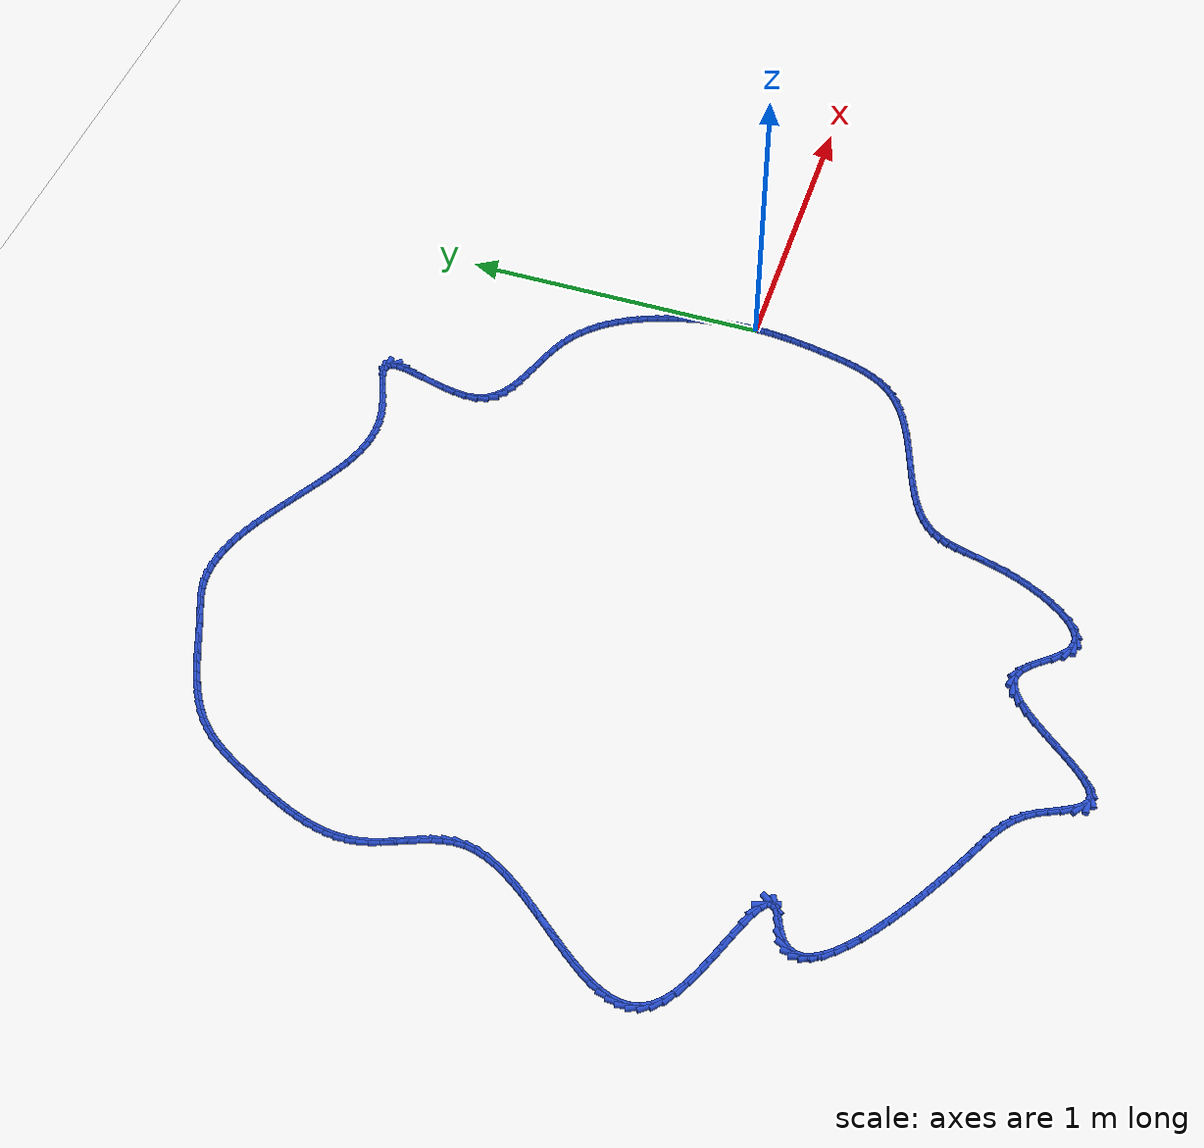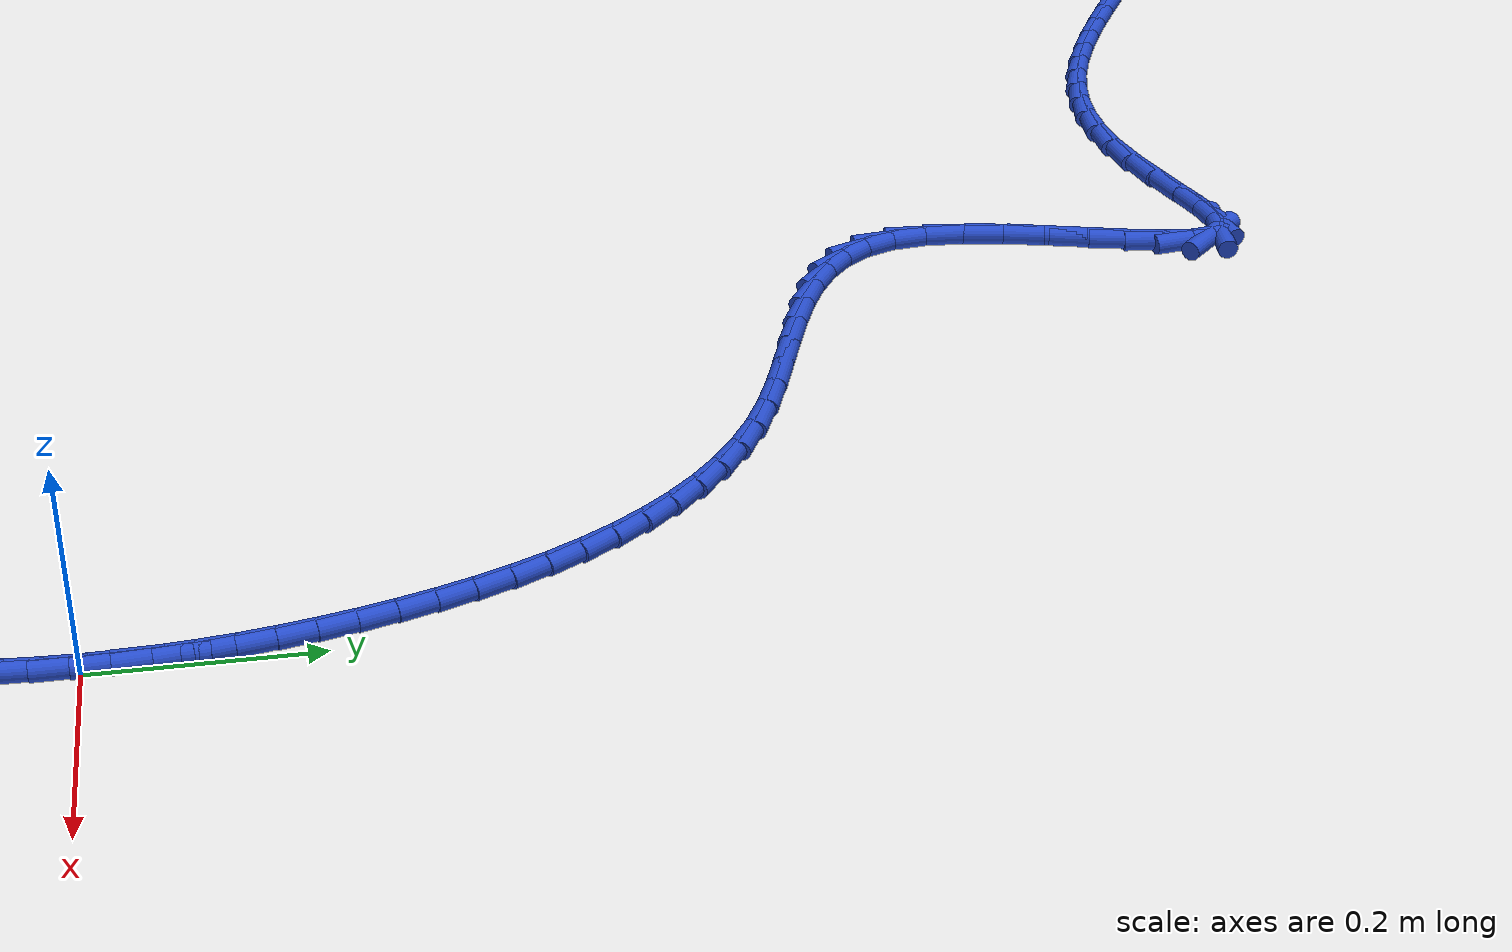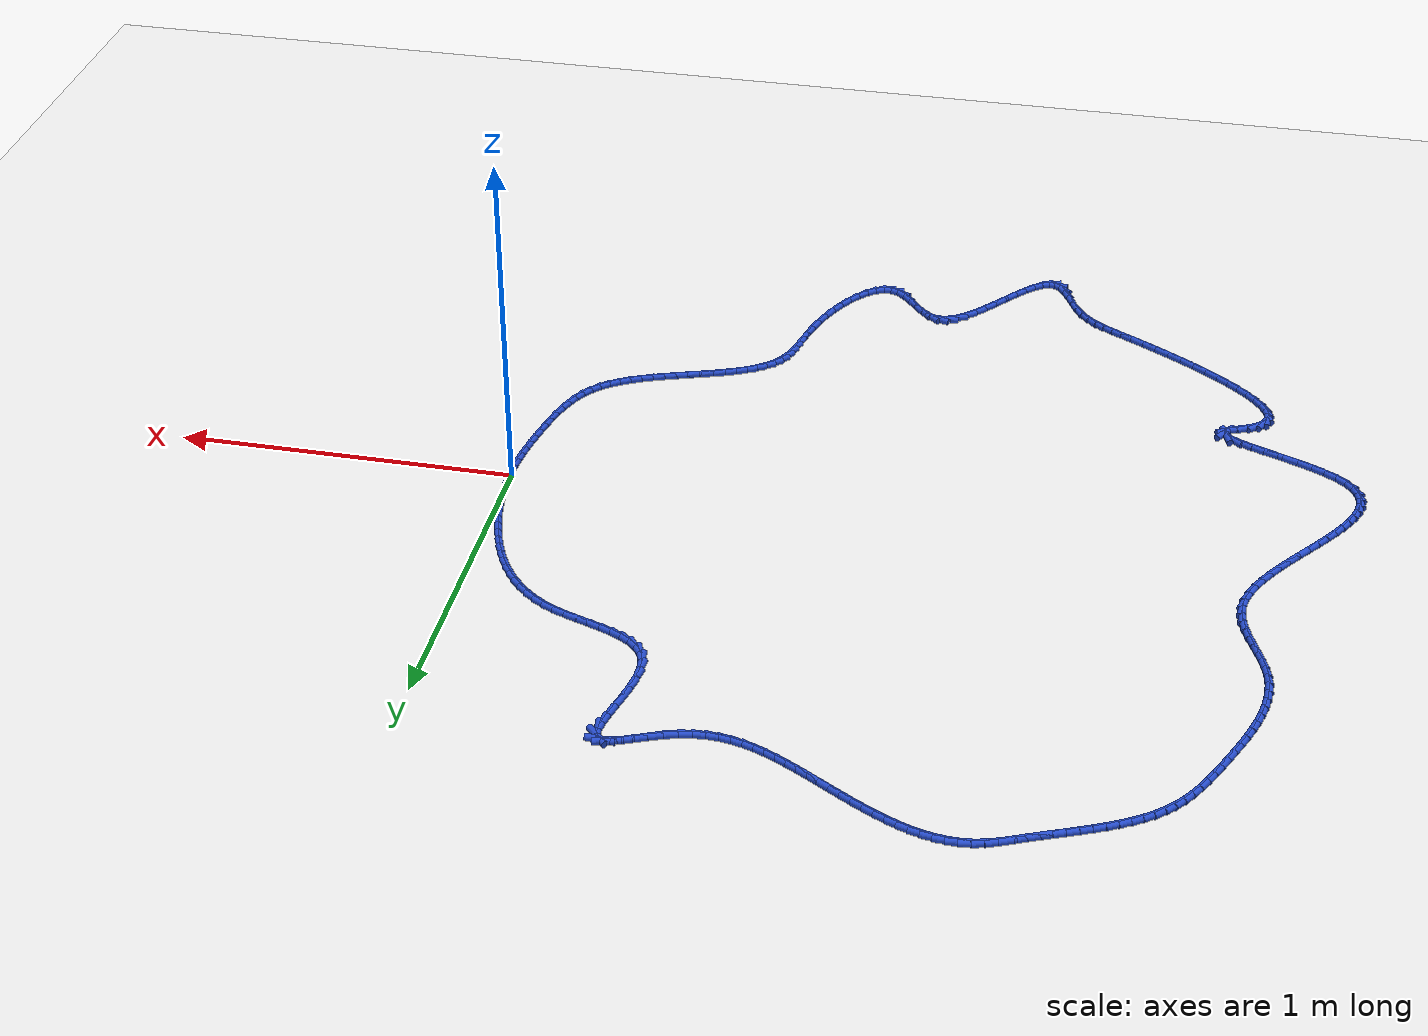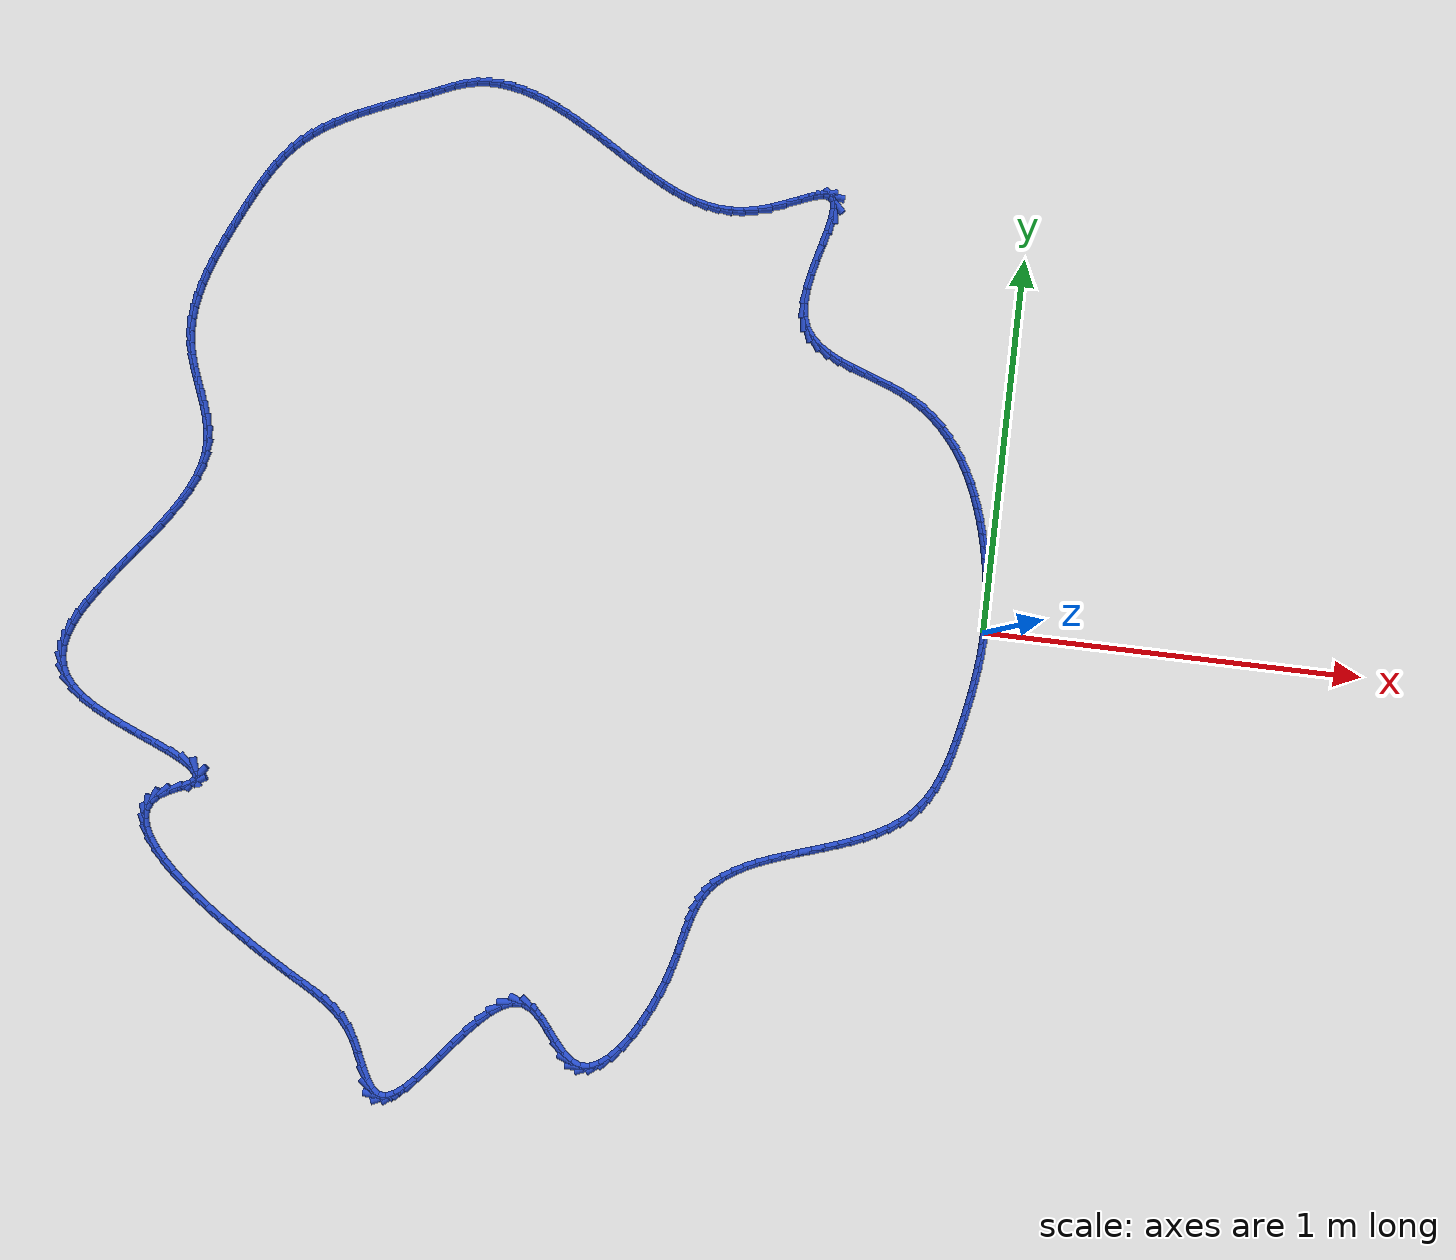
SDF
<sdf version="1.6">
 <world name="default">
  <light name="sun" type="directional">
   <pose>0 0 10 0 -0 0</pose>
   <diffuse>0.8 0.8 0.8 1</diffuse>
   <specular>0.2 0.2 0.2 1</specular>
   <attenuation>
    <range>1000</range>
    <constant>0.9</constant>
    <linear>0.01</linear>
    <quadratic>0.001</quadratic>
   </attenuation>
   <direction>-0.5 0.1 -0.9</direction>
  </light>
  <model name="ground_plane">
   <static>1</static>
   <link name="link">
    <collision name="collision">
     <geometry><plane><normal>0 0 1</normal><size>100 100</size></plane></geometry>
     <surface><friction><ode><mu>100</mu><mu2>50</mu2></ode></friction></surface>
    </collision>
    <visual name="visual">
     <cast_shadows>0</cast_shadows>
     <geometry><plane><normal>0 0 1</normal><size>100 100</size></plane></geometry>
     <material>
      <script><uri>file://media/materials/scripts/gazebo.material</uri><name>Gazebo/WhiteGlow</name></script>
     </material>
    </visual>
   </link>
  </model>
  <gravity>0 0 -9.8</gravity>
  <magnetic_field>6e-06 2.3e-05 -4.2e-05</magnetic_field>
  <atmosphere type="adiabatic"/>
  <physics name="default_physics" default="0" type="ode">
   <max_step_size>0.001</max_step_size>
   <real_time_factor>1</real_time_factor>
   <real_time_update_rate>1000</real_time_update_rate>
  </physics>
  <scene><ambient>0.4 0.4 0.4 1</ambient><background>0.7 0.7 0.7 1</background><shadows>1</shadows></scene>
  <spherical_coordinates>
   <surface_model>EARTH_WGS84</surface_model>
   <latitude_deg>0</latitude_deg>
   <longitude_deg>0</longitude_deg>
   <elevation>0</elevation>
   <heading_deg>0</heading_deg>
  </spherical_coordinates>
  <model name="line">
   <link name="link_0">
    <pose>-1.0408340855860843e-17 5.551115123125783e-17 0.01 0 1.57 -1.564170804574413</pose>
    <collision name="collision">
     <geometry><cylinder><radius>0.01</radius><length>0.08</length></cylinder></geometry>
    </collision>
    <visual name="visual">
     <material>
      <script><name>Gazebo/Blue</name><uri>file://media/materials/scripts/gazebo.material</uri></script>
     </material>
     <geometry><cylinder><radius>0.01</radius><length>0.08</length></cylinder></geometry>
    </visual>
   </link>
   <link name="link_1">
    <pose>-0.00021548872016381447 0.032523559629226366 0.01 0 1.57 -1.5267158604913686</pose>
    <collision name="collision">
     <geometry><cylinder><radius>0.01</radius><length>0.08</length></cylinder></geometry>
    </collision>
    <visual name="visual">
     <material>
      <script><name>Gazebo/Blue</name><uri>file://media/materials/scripts/gazebo.material</uri></script>
     </material>
     <geometry><cylinder><radius>0.01</radius><length>0.08</length></cylinder></geometry>
    </visual>
   </link>
   <link name="link_2">
    <pose>-0.0016531517416874437 0.06511694742671872 0.01 0 1.57 -1.4901632687633821</pose>
    <collision name="collision">
     <geometry><cylinder><radius>0.01</radius><length>0.08</length></cylinder></geometry>
    </collision>
    <visual name="visual">
     <material>
      <script><name>Gazebo/Blue</name><uri>file://media/materials/scripts/gazebo.material</uri></script>
     </material>
     <geometry><cylinder><radius>0.01</radius><length>0.08</length></cylinder></geometry>
    </visual>
   </link>
   <link name="link_3">
    <pose>-0.004291216857513285 0.09776292919291431 0.01 0 1.57 -1.4545378203894928</pose>
    <collision name="collision">
     <geometry><cylinder><radius>0.01</radius><length>0.08</length></cylinder></geometry>
    </collision>
    <visual name="visual">
     <material>
      <script><name>Gazebo/Blue</name><uri>file://media/materials/scripts/gazebo.material</uri></script>
     </material>
     <geometry><cylinder><radius>0.01</radius><length>0.08</length></cylinder></geometry>
    </visual>
   </link>
   <link name="link_4">
    <pose>-0.008107911860583721 0.13044427072825032 0.01 0 1.57 -1.4198543087673157</pose>
    <collision name="collision">
     <geometry><cylinder><radius>0.01</radius><length>0.08</length></cylinder></geometry>
    </collision>
    <visual name="visual">
     <material>
      <script><name>Gazebo/Blue</name><uri>file://media/materials/scripts/gazebo.material</uri></script>
     </material>
     <geometry><cylinder><radius>0.01</radius><length>0.08</length></cylinder></geometry>
    </visual>
   </link>
   <link name="link_5">
    <pose>-0.013081464543841128 0.16314373783316377 0.01 0 1.57 -1.3861184481943685</pose>
    <collision name="collision">
     <geometry><cylinder><radius>0.01</radius><length>0.08</length></cylinder></geometry>
    </collision>
    <visual name="visual">
     <material>
      <script><name>Gazebo/Blue</name><uri>file://media/materials/scripts/gazebo.material</uri></script>
     </material>
     <geometry><cylinder><radius>0.01</radius><length>0.08</length></cylinder></geometry>
    </visual>
   </link>
   <link name="link_6">
    <pose>-0.019190102700227894 0.19584409630809194 0.01 0 1.57 -1.3533278613430586</pose>
    <collision name="collision">
     <geometry><cylinder><radius>0.01</radius><length>0.08</length></cylinder></geometry>
    </collision>
    <visual name="visual">
     <material>
      <script><name>Gazebo/Blue</name><uri>file://media/materials/scripts/gazebo.material</uri></script>
     </material>
     <geometry><cylinder><radius>0.01</radius><length>0.08</length></cylinder></geometry>
    </visual>
   </link>
   <link name="link_7">
    <pose>-0.026412054122686393 0.22852811195347195 0.01 0 1.57 -1.321424288780444</pose>
    <collision name="collision">
     <geometry><cylinder><radius>0.01</radius><length>0.08</length></cylinder></geometry>
    </collision>
    <visual name="visual">
     <material>
      <script><name>Gazebo/Blue</name><uri>file://media/materials/scripts/gazebo.material</uri></script>
     </material>
     <geometry><cylinder><radius>0.01</radius><length>0.08</length></cylinder></geometry>
    </visual>
   </link>
   <link name="link_8">
    <pose>-0.03472683607134908 0.2611769515002711 0.01 0 1.57 -1.2882460721909164</pose>
    <collision name="collision">
     <geometry><cylinder><radius>0.01</radius><length>0.08</length></cylinder></geometry>
    </collision>
    <visual name="visual">
     <material>
      <script><name>Gazebo/Blue</name><uri>file://media/materials/scripts/gazebo.material</uri></script>
     </material>
     <geometry><cylinder><radius>0.01</radius><length>0.08</length></cylinder></geometry>
    </visual>
   </link>
   <link name="link_9">
    <pose>-0.044169640928419185 0.2937027389084428 0.01 0 1.57 -1.2506834093468886</pose>
    <collision name="collision">
     <geometry><cylinder><radius>0.01</radius><length>0.08</length></cylinder></geometry>
    </collision>
    <visual name="visual">
     <material>
      <script><name>Gazebo/Blue</name><uri>file://media/materials/scripts/gazebo.material</uri></script>
     </material>
     <geometry><cylinder><radius>0.01</radius><length>0.08</length></cylinder></geometry>
    </visual>
   </link>
   <link name="link_10">
    <pose>-0.05485136848679792 0.32592371330704156 0.01 0 1.57 -1.208188009615541</pose>
    <collision name="collision">
     <geometry><cylinder><radius>0.01</radius><length>0.08</length></cylinder></geometry>
    </collision>
    <visual name="visual">
     <material>
      <script><name>Gazebo/Blue</name><uri>file://media/materials/scripts/gazebo.material</uri></script>
     </material>
     <geometry><cylinder><radius>0.01</radius><length>0.08</length></cylinder></geometry>
    </visual>
   </link>
   <link name="link_11">
    <pose>-0.0668883334756059 0.3576513987576465 0.01 0 1.57 -1.160390247306412</pose>
    <collision name="collision">
     <geometry><cylinder><radius>0.01</radius><length>0.08</length></cylinder></geometry>
    </collision>
    <visual name="visual">
     <material>
      <script><name>Gazebo/Blue</name><uri>file://media/materials/scripts/gazebo.material</uri></script>
     </material>
     <geometry><cylinder><radius>0.01</radius><length>0.08</length></cylinder></geometry>
    </visual>
   </link>
   <link name="link_12">
    <pose>-0.08039685062396364 0.388697319321836 0.01 0 1.57 -1.1069222254748396</pose>
    <collision name="collision">
     <geometry><cylinder><radius>0.01</radius><length>0.08</length></cylinder></geometry>
    </collision>
    <visual name="visual">
     <material>
      <script><name>Gazebo/Blue</name><uri>file://media/materials/scripts/gazebo.material</uri></script>
     </material>
     <geometry><cylinder><radius>0.01</radius><length>0.08</length></cylinder></geometry>
    </visual>
   </link>
   <link name="link_13">
    <pose>-0.0954932346609917 0.4188729990611888 0.01 0 1.57 -1.0474582827340422</pose>
    <collision name="collision">
     <geometry><cylinder><radius>0.01</radius><length>0.08</length></cylinder></geometry>
    </collision>
    <visual name="visual">
     <material>
      <script><name>Gazebo/Blue</name><uri>file://media/materials/scripts/gazebo.material</uri></script>
     </material>
     <geometry><cylinder><radius>0.01</radius><length>0.08</length></cylinder></geometry>
    </visual>
   </link>
   <link name="link_14">
    <pose>-0.11229380031581063 0.4479899620372835 0.01 0 1.57 -0.9817706041309131</pose>
    <collision name="collision">
     <geometry><cylinder><radius>0.01</radius><length>0.08</length></cylinder></geometry>
    </collision>
    <visual name="visual">
     <material>
      <script><name>Gazebo/Blue</name><uri>file://media/materials/scripts/gazebo.material</uri></script>
     </material>
     <geometry><cylinder><radius>0.01</radius><length>0.08</length></cylinder></geometry>
    </visual>
   </link>
   <link name="link_15">
    <pose>-0.130914862317541 0.4758597323116988 0.01 0 1.57 -0.9097999184941654</pose>
    <collision name="collision">
     <geometry><cylinder><radius>0.01</radius><length>0.08</length></cylinder></geometry>
    </collision>
    <visual name="visual">
     <material>
      <script><name>Gazebo/Blue</name><uri>file://media/materials/scripts/gazebo.material</uri></script>
     </material>
     <geometry><cylinder><radius>0.01</radius><length>0.08</length></cylinder></geometry>
    </visual>
   </link>
   <link name="link_16">
    <pose>-0.15147273539530337 0.5022938339460133 0.01 0 1.57 -0.83173599106406</pose>
    <collision name="collision">
     <geometry><cylinder><radius>0.01</radius><length>0.08</length></cylinder></geometry>
    </collision>
    <visual name="visual">
     <material>
      <script><name>Gazebo/Blue</name><uri>file://media/materials/scripts/gazebo.material</uri></script>
     </material>
     <geometry><cylinder><radius>0.01</radius><length>0.08</length></cylinder></geometry>
    </visual>
   </link>
   <link name="link_17">
    <pose>-0.17408373427821833 0.5271037910018059 0.01 0 1.57 -0.7480947168603113</pose>
    <collision name="collision">
     <geometry><cylinder><radius>0.01</radius><length>0.08</length></cylinder></geometry>
    </collision>
    <visual name="visual">
     <material>
      <script><name>Gazebo/Blue</name><uri>file://media/materials/scripts/gazebo.material</uri></script>
     </material>
     <geometry><cylinder><radius>0.01</radius><length>0.08</length></cylinder></geometry>
    </visual>
   </link>
   <link name="link_18">
    <pose>-0.19886417369540638 0.550101127540655 0.01 0 1.57 -0.6597701512960921</pose>
    <collision name="collision">
     <geometry><cylinder><radius>0.01</radius><length>0.08</length></cylinder></geometry>
    </collision>
    <visual name="visual">
     <material>
      <script><name>Gazebo/Blue</name><uri>file://media/materials/scripts/gazebo.material</uri></script>
     </material>
     <geometry><cylinder><radius>0.01</radius><length>0.08</length></cylinder></geometry>
    </visual>
   </link>
   <link name="link_19">
    <pose>-0.22593036837598804 0.5710973676241394 0.01 0 1.57 -0.5680356999523042</pose>
    <collision name="collision">
     <geometry><cylinder><radius>0.01</radius><length>0.08</length></cylinder></geometry>
    </collision>
    <visual name="visual">
     <material>
      <script><name>Gazebo/Blue</name><uri>file://media/materials/scripts/gazebo.material</uri></script>
     </material>
     <geometry><cylinder><radius>0.01</radius><length>0.08</length></cylinder></geometry>
    </visual>
   </link>
   <link name="link_20">
    <pose>-0.255398633049084 0.5899040353138376 0.01 0 1.57 -0.4751199236134291</pose>
    <collision name="collision">
     <geometry><cylinder><radius>0.01</radius><length>0.08</length></cylinder></geometry>
    </collision>
    <visual name="visual">
     <material>
      <script><name>Gazebo/Blue</name><uri>file://media/materials/scripts/gazebo.material</uri></script>
     </material>
     <geometry><cylinder><radius>0.01</radius><length>0.08</length></cylinder></geometry>
    </visual>
   </link>
   <link name="link_21">
    <pose>-0.2873666610249024 0.6063491485619591 0.01 0 1.57 -0.39850162706115866</pose>
    <collision name="collision">
     <geometry><cylinder><radius>0.01</radius><length>0.08</length></cylinder></geometry>
    </collision>
    <visual name="visual">
     <material>
      <script><name>Gazebo/Blue</name><uri>file://media/materials/scripts/gazebo.material</uri></script>
     </material>
     <geometry><cylinder><radius>0.01</radius><length>0.08</length></cylinder></geometry>
    </visual>
   </link>
   <link name="link_22">
    <pose>-0.3214412702870145 0.6206955173195821 0.01 0 1.57 -0.35269231981375615</pose>
    <collision name="collision">
     <geometry><cylinder><radius>0.01</radius><length>0.08</length></cylinder></geometry>
    </collision>
    <visual name="visual">
     <material>
      <script><name>Gazebo/Blue</name><uri>file://media/materials/scripts/gazebo.material</uri></script>
     </material>
     <geometry><cylinder><radius>0.01</radius><length>0.08</length></cylinder></geometry>
    </visual>
   </link>
   <link name="link_23">
    <pose>-0.3567008920000841 0.6336739692781433 0.01 0 1.57 -0.3351829775562453</pose>
    <collision name="collision">
     <geometry><cylinder><radius>0.01</radius><length>0.08</length></cylinder></geometry>
    </collision>
    <visual name="visual">
     <material>
      <script><name>Gazebo/Blue</name><uri>file://media/materials/scripts/gazebo.material</uri></script>
     </material>
     <geometry><cylinder><radius>0.01</radius><length>0.08</length></cylinder></geometry>
    </visual>
   </link>
   <link name="link_24">
    <pose>-0.39219782085605287 0.6460384824660403 0.01 0 1.57 -0.345082191216047</pose>
    <collision name="collision">
     <geometry><cylinder><radius>0.01</radius><length>0.08</length></cylinder></geometry>
    </collision>
    <visual name="visual">
     <material>
      <script><name>Gazebo/Blue</name><uri>file://media/materials/scripts/gazebo.material</uri></script>
     </material>
     <geometry><cylinder><radius>0.01</radius><length>0.08</length></cylinder></geometry>
    </visual>
   </link>
   <link name="link_25">
    <pose>-0.426984351546863 0.6585430349116712 0.01 0 1.57 -0.3843309115429505</pose>
    <collision name="collision">
     <geometry><cylinder><radius>0.01</radius><length>0.08</length></cylinder></geometry>
    </collision>
    <visual name="visual">
     <material>
      <script><name>Gazebo/Blue</name><uri>file://media/materials/scripts/gazebo.material</uri></script>
     </material>
     <geometry><cylinder><radius>0.01</radius><length>0.08</length></cylinder></geometry>
    </visual>
   </link>
   <link name="link_26">
    <pose>-0.4601127787644565 0.6719416046434337 0.01 0 1.57 -0.458003324438978</pose>
    <collision name="collision">
     <geometry><cylinder><radius>0.01</radius><length>0.08</length></cylinder></geometry>
    </collision>
    <visual name="visual">
     <material>
      <script><name>Gazebo/Blue</name><uri>file://media/materials/scripts/gazebo.material</uri></script>
     </material>
     <geometry><cylinder><radius>0.01</radius><length>0.08</length></cylinder></geometry>
    </visual>
   </link>
   <link name="link_27">
    <pose>-0.4906353972007751 0.6869881696897255 0.01 0 1.57 -0.5742510252359123</pose>
    <collision name="collision">
     <geometry><cylinder><radius>0.01</radius><length>0.08</length></cylinder></geometry>
    </collision>
    <visual name="visual">
     <material>
      <script><name>Gazebo/Blue</name><uri>file://media/materials/scripts/gazebo.material</uri></script>
     </material>
     <geometry><cylinder><radius>0.01</radius><length>0.08</length></cylinder></geometry>
    </visual>
   </link>
   <link name="link_28">
    <pose>-0.5176045015477615 0.704436708078945 0.01 0 1.57 -0.7421631665555947</pose>
    <collision name="collision">
     <geometry><cylinder><radius>0.01</radius><length>0.08</length></cylinder></geometry>
    </collision>
    <visual name="visual">
     <material>
      <script><name>Gazebo/Blue</name><uri>file://media/materials/scripts/gazebo.material</uri></script>
     </material>
     <geometry><cylinder><radius>0.01</radius><length>0.08</length></cylinder></geometry>
    </visual>
   </link>
   <link name="link_29">
    <pose>-0.5400723864973574 0.7250411978394897 0.01 0 1.57 -0.963944680451375</pose>
    <collision name="collision">
     <geometry><cylinder><radius>0.01</radius><length>0.08</length></cylinder></geometry>
    </collision>
    <visual name="visual">
     <material>
      <script><name>Gazebo/Blue</name><uri>file://media/materials/scripts/gazebo.material</uri></script>
     </material>
     <geometry><cylinder><radius>0.01</radius><length>0.08</length></cylinder></geometry>
    </visual>
   </link>
   <link name="link_30">
    <pose>-0.557091346741505 0.7495556169997577 0.01 0 1.57 -1.2216612405446048</pose>
    <collision name="collision">
     <geometry><cylinder><radius>0.01</radius><length>0.08</length></cylinder></geometry>
    </collision>
    <visual name="visual">
     <material>
      <script><name>Gazebo/Blue</name><uri>file://media/materials/scripts/gazebo.material</uri></script>
     </material>
     <geometry><cylinder><radius>0.01</radius><length>0.08</length></cylinder></geometry>
    </visual>
   </link>
   <link name="link_31">
    <pose>-0.567713676972146 0.7787339435881467 0.01 0 1.57 -1.4677217655302628</pose>
    <collision name="collision">
     <geometry><cylinder><radius>0.01</radius><length>0.08</length></cylinder></geometry>
    </collision>
    <visual name="visual">
     <material>
      <script><name>Gazebo/Blue</name><uri>file://media/materials/scripts/gazebo.material</uri></script>
     </material>
     <geometry><cylinder><radius>0.01</radius><length>0.08</length></cylinder></geometry>
    </visual>
   </link>
   <link name="link_32">
    <pose>-0.5712664481055553 0.8130797626722868 0.01 0 1.57 1.5065172757214418</pose>
    <collision name="collision">
     <geometry><cylinder><radius>0.01</radius><length>0.08</length></cylinder></geometry>
    </collision>
    <visual name="visual">
     <material>
      <script><name>Gazebo/Blue</name><uri>file://media/materials/scripts/gazebo.material</uri></script>
     </material>
     <geometry><cylinder><radius>0.01</radius><length>0.08</length></cylinder></geometry>
    </visual>
   </link>
   <link name="link_33">
    <pose>-0.5687912159521845 0.8515343154529437 0.01 0 1.57 1.4060175882886885</pose>
    <collision name="collision">
     <geometry><cylinder><radius>0.01</radius><length>0.08</length></cylinder></geometry>
    </collision>
    <visual name="visual">
     <material>
      <script><name>Gazebo/Blue</name><uri>file://media/materials/scripts/gazebo.material</uri></script>
     </material>
     <geometry><cylinder><radius>0.01</radius><length>0.08</length></cylinder></geometry>
    </visual>
   </link>
   <link name="link_34">
    <pose>-0.5619895930285571 0.8924373589474927 0.01 0 1.57 1.3484602443475313</pose>
    <collision name="collision">
     <geometry><cylinder><radius>0.01</radius><length>0.08</length></cylinder></geometry>
    </collision>
    <visual name="visual">
     <material>
      <script><name>Gazebo/Blue</name><uri>file://media/materials/scripts/gazebo.material</uri></script>
     </material>
     <geometry><cylinder><radius>0.01</radius><length>0.08</length></cylinder></geometry>
    </visual>
   </link>
   <link name="link_35">
    <pose>-0.5525645779636124 0.9341273870625975 0.01 0 1.57 1.3225567108189606</pose>
    <collision name="collision">
     <geometry><cylinder><radius>0.01</radius><length>0.08</length></cylinder></geometry>
    </collision>
    <visual name="visual">
     <material>
      <script><name>Gazebo/Blue</name><uri>file://media/materials/scripts/gazebo.material</uri></script>
     </material>
     <geometry><cylinder><radius>0.01</radius><length>0.08</length></cylinder></geometry>
    </visual>
   </link>
   <link name="link_36">
    <pose>-0.5422191693862908 0.9749428937049223 0.01 0 1.57 1.325991410335295</pose>
    <collision name="collision">
     <geometry><cylinder><radius>0.01</radius><length>0.08</length></cylinder></geometry>
    </collision>
    <visual name="visual">
     <material>
      <script><name>Gazebo/Blue</name><uri>file://media/materials/scripts/gazebo.material</uri></script>
     </material>
     <geometry><cylinder><radius>0.01</radius><length>0.08</length></cylinder></geometry>
    </visual>
   </link>
   <link name="link_37">
    <pose>-0.5326563659255316 1.0132223727811307 0.01 0 1.57 1.3660535796439837</pose>
    <collision name="collision">
     <geometry><cylinder><radius>0.01</radius><length>0.08</length></cylinder></geometry>
    </collision>
    <visual name="visual">
     <material>
      <script><name>Gazebo/Blue</name><uri>file://media/materials/scripts/gazebo.material</uri></script>
     </material>
     <geometry><cylinder><radius>0.01</radius><length>0.08</length></cylinder></geometry>
    </visual>
   </link>
   <link name="link_38">
    <pose>-0.5255791662102745 1.0473043181978867 0.01 0 1.57 1.468802085061709</pose>
    <collision name="collision">
     <geometry><cylinder><radius>0.01</radius><length>0.08</length></cylinder></geometry>
    </collision>
    <visual name="visual">
     <material>
      <script><name>Gazebo/Blue</name><uri>file://media/materials/scripts/gazebo.material</uri></script>
     </material>
     <geometry><cylinder><radius>0.01</radius><length>0.08</length></cylinder></geometry>
    </visual>
   </link>
   <link name="link_39">
    <pose>-0.5226905688694596 1.075527223861855 0.01 0 1.57 -1.4267449566413157</pose>
    <collision name="collision">
     <geometry><cylinder><radius>0.01</radius><length>0.08</length></cylinder></geometry>
    </collision>
    <visual name="visual">
     <material>
      <script><name>Gazebo/Blue</name><uri>file://media/materials/scripts/gazebo.material</uri></script>
     </material>
     <geometry><cylinder><radius>0.01</radius><length>0.08</length></cylinder></geometry>
    </visual>
   </link>
   <link name="link_40">
    <pose>-0.5256935725320268 1.096229583679699 0.01 0 1.57 -0.8270915157916727</pose>
    <collision name="collision">
     <geometry><cylinder><radius>0.01</radius><length>0.08</length></cylinder></geometry>
    </collision>
    <visual name="visual">
     <material>
      <script><name>Gazebo/Blue</name><uri>file://media/materials/scripts/gazebo.material</uri></script>
     </material>
     <geometry><cylinder><radius>0.01</radius><length>0.08</length></cylinder></geometry>
    </visual>
   </link>
   <link name="link_41">
    <pose>-0.5362911758269155 1.1077498915580826 0.01 0 1.57 -0.06721329275596687</pose>
    <collision name="collision">
     <geometry><cylinder><radius>0.01</radius><length>0.08</length></cylinder></geometry>
    </collision>
    <visual name="visual">
     <material>
      <script><name>Gazebo/Blue</name><uri>file://media/materials/scripts/gazebo.material</uri></script>
     </material>
     <geometry><cylinder><radius>0.01</radius><length>0.08</length></cylinder></geometry>
    </visual>
   </link>
   <link name="link_42">
    <pose>-0.5556733424497363 1.1090545961122473 0.01 0 1.57 0.25269013360167036</pose>
    <collision name="collision">
     <geometry><cylinder><radius>0.01</radius><length>0.08</length></cylinder></geometry>
    </collision>
    <visual name="visual">
     <material>
      <script><name>Gazebo/Blue</name><uri>file://media/materials/scripts/gazebo.material</uri></script>
     </material>
     <geometry><cylinder><radius>0.01</radius><length>0.08</length></cylinder></geometry>
    </visual>
   </link>
   <link name="link_43">
    <pose>-0.5825820153563831 1.102106523105138 0.01 0 1.57 0.3635547472799359</pose>
    <collision name="collision">
     <geometry><cylinder><radius>0.01</radius><length>0.08</length></cylinder></geometry>
    </collision>
    <visual name="visual">
     <material>
      <script><name>Gazebo/Blue</name><uri>file://media/materials/scripts/gazebo.material</uri></script>
     </material>
     <geometry><cylinder><radius>0.01</radius><length>0.08</length></cylinder></geometry>
    </visual>
   </link>
   <link name="link_44">
    <pose>-0.6150297826313605 1.0897612285914537 0.01 0 1.57 0.39211564461522525</pose>
    <collision name="collision">
     <geometry><cylinder><radius>0.01</radius><length>0.08</length></cylinder></geometry>
    </collision>
    <visual name="visual">
     <material>
      <script><name>Gazebo/Blue</name><uri>file://media/materials/scripts/gazebo.material</uri></script>
     </material>
     <geometry><cylinder><radius>0.01</radius><length>0.08</length></cylinder></geometry>
    </visual>
   </link>
   <link name="link_45">
    <pose>-0.6510291080634547 1.0748744207638434 0.01 0 1.57 0.37007345212906</pose>
    <collision name="collision">
     <geometry><cylinder><radius>0.01</radius><length>0.08</length></cylinder></geometry>
    </collision>
    <visual name="visual">
     <material>
      <script><name>Gazebo/Blue</name><uri>file://media/materials/scripts/gazebo.material</uri></script>
     </material>
     <geometry><cylinder><radius>0.01</radius><length>0.08</length></cylinder></geometry>
    </visual>
   </link>
   <link name="link_46">
    <pose>-0.6885924554414511 1.0603018078149564 0.01 0 1.57 0.29863229330039986</pose>
    <collision name="collision">
     <geometry><cylinder><radius>0.01</radius><length>0.08</length></cylinder></geometry>
    </collision>
    <visual name="visual">
     <material>
      <script><name>Gazebo/Blue</name><uri>file://media/materials/scripts/gazebo.material</uri></script>
     </material>
     <geometry><cylinder><radius>0.01</radius><length>0.08</length></cylinder></geometry>
    </visual>
   </link>
   <link name="link_47">
    <pose>-0.7257577996019973 1.0488608913991415 0.01 0 1.57 0.1899999498678007</pose>
    <collision name="collision">
     <geometry><cylinder><radius>0.01</radius><length>0.08</length></cylinder></geometry>
    </collision>
    <visual name="visual">
     <material>
      <script><name>Gazebo/Blue</name><uri>file://media/materials/scripts/gazebo.material</uri></script>
     </material>
     <geometry><cylinder><radius>0.01</radius><length>0.08</length></cylinder></geometry>
    </visual>
   </link>
   <link name="link_48">
    <pose>-0.7614839824579925 1.0419900395730777 0.01 0 1.57 0.07528380188945365</pose>
    <collision name="collision">
     <geometry><cylinder><radius>0.01</radius><length>0.08</length></cylinder></geometry>
    </collision>
    <visual name="visual">
     <material>
      <script><name>Gazebo/Blue</name><uri>file://media/materials/scripts/gazebo.material</uri></script>
     </material>
     <geometry><cylinder><radius>0.01</radius><length>0.08</length></cylinder></geometry>
    </visual>
   </link>
   <link name="link_49">
    <pose>-0.7958866251549587 1.0393951737179805 0.01 0 1.57 -0.03836672406796584</pose>
    <collision name="collision">
     <geometry><cylinder><radius>0.01</radius><length>0.08</length></cylinder></geometry>
    </collision>
    <visual name="visual">
     <material>
      <script><name>Gazebo/Blue</name><uri>file://media/materials/scripts/gazebo.material</uri></script>
     </material>
     <geometry><cylinder><radius>0.01</radius><length>0.08</length></cylinder></geometry>
    </visual>
   </link>
   <link name="link_50">
    <pose>-0.8291548130623894 1.0406721917576973 0.01 0 1.57 -0.14575315261627442</pose>
    <collision name="collision">
     <geometry><cylinder><radius>0.01</radius><length>0.08</length></cylinder></geometry>
    </collision>
    <visual name="visual">
     <material>
      <script><name>Gazebo/Blue</name><uri>file://media/materials/scripts/gazebo.material</uri></script>
     </material>
     <geometry><cylinder><radius>0.01</radius><length>0.08</length></cylinder></geometry>
    </visual>
   </link>
   <link name="link_51">
    <pose>-0.8614776315497779 1.045416991616076 0.01 0 1.57 -0.24249784045132938</pose>
    <collision name="collision">
     <geometry><cylinder><radius>0.01</radius><length>0.08</length></cylinder></geometry>
    </collision>
    <visual name="visual">
     <material>
      <script><name>Gazebo/Blue</name><uri>file://media/materials/scripts/gazebo.material</uri></script>
     </material>
     <geometry><cylinder><radius>0.01</radius><length>0.08</length></cylinder></geometry>
    </visual>
   </link>
   <link name="link_52">
    <pose>-0.8930441659866172 1.053225471216963 0.01 0 1.57 -0.32566327671614204</pose>
    <collision name="collision">
     <geometry><cylinder><radius>0.01</radius><length>0.08</length></cylinder></geometry>
    </collision>
    <visual name="visual">
     <material>
      <script><name>Gazebo/Blue</name><uri>file://media/materials/scripts/gazebo.material</uri></script>
     </material>
     <geometry><cylinder><radius>0.01</radius><length>0.08</length></cylinder></geometry>
    </visual>
   </link>
   <link name="link_53">
    <pose>-0.9240435017424012 1.0636935284842075 0.01 0 1.57 -0.39380818073051244</pose>
    <collision name="collision">
     <geometry><cylinder><radius>0.01</radius><length>0.08</length></cylinder></geometry>
    </collision>
    <visual name="visual">
     <material>
      <script><name>Gazebo/Blue</name><uri>file://media/materials/scripts/gazebo.material</uri></script>
     </material>
     <geometry><cylinder><radius>0.01</radius><length>0.08</length></cylinder></geometry>
    </visual>
   </link>
   <link name="link_54">
    <pose>-0.9546647241866232 1.076417061341655 0.01 0 1.57 -0.4466503895187564</pose>
    <collision name="collision">
     <geometry><cylinder><radius>0.01</radius><length>0.08</length></cylinder></geometry>
    </collision>
    <visual name="visual">
     <material>
      <script><name>Gazebo/Blue</name><uri>file://media/materials/scripts/gazebo.material</uri></script>
     </material>
     <geometry><cylinder><radius>0.01</radius><length>0.08</length></cylinder></geometry>
    </visual>
   </link>
   <link name="link_55">
    <pose>-0.9850969186887767 1.0909919677131548 0.01 0 1.57 -0.4846796203394419</pose>
    <collision name="collision">
     <geometry><cylinder><radius>0.01</radius><length>0.08</length></cylinder></geometry>
    </collision>
    <visual name="visual">
     <material>
      <script><name>Gazebo/Blue</name><uri>file://media/materials/scripts/gazebo.material</uri></script>
     </material>
     <geometry><cylinder><radius>0.01</radius><length>0.08</length></cylinder></geometry>
    </visual>
   </link>
   <link name="link_56">
    <pose>-1.0155265908356563 1.1070154229758058 0.01 0 1.57 -0.5109127465685978</pose>
    <collision name="collision">
     <geometry><cylinder><radius>0.01</radius><length>0.08</length></cylinder></geometry>
    </collision>
    <visual name="visual">
     <material>
      <script><name>Gazebo/Blue</name><uri>file://media/materials/scripts/gazebo.material</uri></script>
     </material>
     <geometry><cylinder><radius>0.01</radius><length>0.08</length></cylinder></geometry>
    </visual>
   </link>
   <link name="link_57">
    <pose>-1.0460535395283852 1.124127537804218 0.01 0 1.57 -0.5288578066641408</pose>
    <collision name="collision">
     <geometry><cylinder><radius>0.01</radius><length>0.08</length></cylinder></geometry>
    </collision>
    <visual name="visual">
     <material>
      <script><name>Gazebo/Blue</name><uri>file://media/materials/scripts/gazebo.material</uri></script>
     </material>
     <geometry><cylinder><radius>0.01</radius><length>0.08</length></cylinder></geometry>
    </visual>
   </link>
   <link name="link_58">
    <pose>-1.076672210981516 1.1420205912716215 0.01 0 1.57 -0.539228829341392</pose>
    <collision name="collision">
     <geometry><cylinder><radius>0.01</radius><length>0.08</length></cylinder></geometry>
    </collision>
    <visual name="visual">
     <material>
      <script><name>Gazebo/Blue</name><uri>file://media/materials/scripts/gazebo.material</uri></script>
     </material>
     <geometry><cylinder><radius>0.01</radius><length>0.08</length></cylinder></geometry>
    </visual>
   </link>
   <link name="link_59">
    <pose>-1.107370698017706 1.1603900085151178 0.01 0 1.57 -0.5423618878432978</pose>
    <collision name="collision">
     <geometry><cylinder><radius>0.01</radius><length>0.08</length></cylinder></geometry>
    </collision>
    <visual name="visual">
     <material>
      <script><name>Gazebo/Blue</name><uri>file://media/materials/scripts/gazebo.material</uri></script>
     </material>
     <geometry><cylinder><radius>0.01</radius><length>0.08</length></cylinder></geometry>
    </visual>
   </link>
   <link name="link_60">
    <pose>-1.1381370934596116 1.1789312146718092 0.01 0 1.57 -0.538388861175772</pose>
    <collision name="collision">
     <geometry><cylinder><radius>0.01</radius><length>0.08</length></cylinder></geometry>
    </collision>
    <visual name="visual">
     <material>
      <script><name>Gazebo/Blue</name><uri>file://media/materials/scripts/gazebo.material</uri></script>
     </material>
     <geometry><cylinder><radius>0.01</radius><length>0.08</length></cylinder></geometry>
    </visual>
   </link>
   <link name="link_61">
    <pose>-1.1689594901298903 1.1973396348787975 0.01 0 1.57 -0.5272426746919803</pose>
    <collision name="collision">
     <geometry><cylinder><radius>0.01</radius><length>0.08</length></cylinder></geometry>
    </collision>
    <visual name="visual">
     <material>
      <script><name>Gazebo/Blue</name><uri>file://media/materials/scripts/gazebo.material</uri></script>
     </material>
     <geometry><cylinder><radius>0.01</radius><length>0.08</length></cylinder></geometry>
    </visual>
   </link>
   <link name="link_62">
    <pose>-1.1998259808511984 1.2153106942731842 0.01 0 1.57 -0.508659933239682</pose>
    <collision name="collision">
     <geometry><cylinder><radius>0.01</radius><length>0.08</length></cylinder></geometry>
    </collision>
    <visual name="visual">
     <material>
      <script><name>Gazebo/Blue</name><uri>file://media/materials/scripts/gazebo.material</uri></script>
     </material>
     <geometry><cylinder><radius>0.01</radius><length>0.08</length></cylinder></geometry>
    </visual>
   </link>
   <link name="link_63">
    <pose>-1.2307246584461935 1.2325398179920721 0.01 0 1.57 -0.48218251883578617</pose>
    <collision name="collision">
     <geometry><cylinder><radius>0.01</radius><length>0.08</length></cylinder></geometry>
    </collision>
    <visual name="visual">
     <material>
      <script><name>Gazebo/Blue</name><uri>file://media/materials/scripts/gazebo.material</uri></script>
     </material>
     <geometry><cylinder><radius>0.01</radius><length>0.08</length></cylinder></geometry>
    </visual>
   </link>
   <link name="link_64">
    <pose>-1.2616436157375317 1.2487224311725627 0.01 0 1.57 -0.447162766416436</pose>
    <collision name="collision">
     <geometry><cylinder><radius>0.01</radius><length>0.08</length></cylinder></geometry>
    </collision>
    <visual name="visual">
     <material>
      <script><name>Gazebo/Blue</name><uri>file://media/materials/scripts/gazebo.material</uri></script>
     </material>
     <geometry><cylinder><radius>0.01</radius><length>0.08</length></cylinder></geometry>
    </visual>
   </link>
   <link name="link_65">
    <pose>-1.2925709455478702 1.263553958951758 0.01 0 1.57 -0.40278114426702993</pose>
    <collision name="collision">
     <geometry><cylinder><radius>0.01</radius><length>0.08</length></cylinder></geometry>
    </collision>
    <visual name="visual">
     <material>
      <script><name>Gazebo/Blue</name><uri>file://media/materials/scripts/gazebo.material</uri></script>
     </material>
     <geometry><cylinder><radius>0.01</radius><length>0.08</length></cylinder></geometry>
    </visual>
   </link>
   <link name="link_66">
    <pose>-1.3234947406998665 1.2767298264667601 0.01 0 1.57 -0.3480916377065569</pose>
    <collision name="collision">
     <geometry><cylinder><radius>0.01</radius><length>0.08</length></cylinder></geometry>
    </collision>
    <visual name="visual">
     <material>
      <script><name>Gazebo/Blue</name><uri>file://media/materials/scripts/gazebo.material</uri></script>
     </material>
     <geometry><cylinder><radius>0.01</radius><length>0.08</length></cylinder></geometry>
    </visual>
   </link>
   <link name="link_67">
    <pose>-1.3544030940161766 1.2879454588546708 0.01 0 1.57 -0.28211795650158694</pose>
    <collision name="collision">
     <geometry><cylinder><radius>0.01</radius><length>0.08</length></cylinder></geometry>
    </collision>
    <visual name="visual">
     <material>
      <script><name>Gazebo/Blue</name><uri>file://media/materials/scripts/gazebo.material</uri></script>
     </material>
     <geometry><cylinder><radius>0.01</radius><length>0.08</length></cylinder></geometry>
    </visual>
   </link>
   <link name="link_68">
    <pose>-1.3852840983194574 1.296896281252592 0.01 0 1.57 -0.20402998788747975</pose>
    <collision name="collision">
     <geometry><cylinder><radius>0.01</radius><length>0.08</length></cylinder></geometry>
    </collision>
    <visual name="visual">
     <material>
      <script><name>Gazebo/Blue</name><uri>file://media/materials/scripts/gazebo.material</uri></script>
     </material>
     <geometry><cylinder><radius>0.01</radius><length>0.08</length></cylinder></geometry>
    </visual>
   </link>
   <link name="link_69">
    <pose>-1.4161258464323665 1.3032777187976257 0.01 0 1.57 -0.1134250429588424</pose>
    <collision name="collision">
     <geometry><cylinder><radius>0.01</radius><length>0.08</length></cylinder></geometry>
    </collision>
    <visual name="visual">
     <material>
      <script><name>Gazebo/Blue</name><uri>file://media/materials/scripts/gazebo.material</uri></script>
     </material>
     <geometry><cylinder><radius>0.01</radius><length>0.08</length></cylinder></geometry>
    </visual>
   </link>
   <link name="link_70">
    <pose>-1.4469164311775604 1.3067851966268738 0.01 0 1.57 -0.010704760677421188</pose>
    <collision name="collision">
     <geometry><cylinder><radius>0.01</radius><length>0.08</length></cylinder></geometry>
    </collision>
    <visual name="visual">
     <material>
      <script><name>Gazebo/Blue</name><uri>file://media/materials/scripts/gazebo.material</uri></script>
     </material>
     <geometry><cylinder><radius>0.01</radius><length>0.08</length></cylinder></geometry>
    </visual>
   </link>
   <link name="link_71">
    <pose>-1.4776439453776957 1.3071141398774384 0.01 0 1.57 0.10253975923354064</pose>
    <collision name="collision">
     <geometry><cylinder><radius>0.01</radius><length>0.08</length></cylinder></geometry>
    </collision>
    <visual name="visual">
     <material>
      <script><name>Gazebo/Blue</name><uri>file://media/materials/scripts/gazebo.material</uri></script>
     </material>
     <geometry><cylinder><radius>0.01</radius><length>0.08</length></cylinder></geometry>
    </visual>
   </link>
   <link name="link_72">
    <pose>-1.5082964818554294 1.3039599736864214 0.01 0 1.57 0.22310440724811872</pose>
    <collision name="collision">
     <geometry><cylinder><radius>0.01</radius><length>0.08</length></cylinder></geometry>
    </collision>
    <visual name="visual">
     <material>
      <script><name>Gazebo/Blue</name><uri>file://media/materials/scripts/gazebo.material</uri></script>
     </material>
     <geometry><cylinder><radius>0.01</radius><length>0.08</length></cylinder></geometry>
    </visual>
   </link>
   <link name="link_73">
    <pose>-1.5388628648128941 1.297025031713841 0.01 0 1.57 0.3295399120203999</pose>
    <collision name="collision">
     <geometry><cylinder><radius>0.01</radius><length>0.08</length></cylinder></geometry>
    </collision>
    <visual name="visual">
     <material>
      <script><name>Gazebo/Blue</name><uri>file://media/materials/scripts/gazebo.material</uri></script>
     </material>
     <geometry><cylinder><radius>0.01</radius><length>0.08</length></cylinder></geometry>
    </visual>
   </link>
   <link name="link_74">
    <pose>-1.5693924663470862 1.28658357578187 0.01 0 1.57 0.3923643624764167</pose>
    <collision name="collision">
     <geometry><cylinder><radius>0.01</radius><length>0.08</length></cylinder></geometry>
    </collision>
    <visual name="visual">
     <material>
      <script><name>Gazebo/Blue</name><uri>file://media/materials/scripts/gazebo.material</uri></script>
     </material>
     <geometry><cylinder><radius>0.01</radius><length>0.08</length></cylinder></geometry>
    </visual>
   </link>
   <link name="link_75">
    <pose>-1.6000396001915544 1.2739011338411081 0.01 0 1.57 0.4131552980902998</pose>
    <collision name="collision">
     <geometry><cylinder><radius>0.01</radius><length>0.08</length></cylinder></geometry>
    </collision>
    <visual name="visual">
     <material>
      <script><name>Gazebo/Blue</name><uri>file://media/materials/scripts/gazebo.material</uri></script>
     </material>
     <geometry><cylinder><radius>0.01</radius><length>0.08</length></cylinder></geometry>
    </visual>
   </link>
   <link name="link_76">
    <pose>-1.6309690410488726 1.2603420469025084 0.01 0 1.57 0.40258670472709024</pose>
    <collision name="collision">
     <geometry><cylinder><radius>0.01</radius><length>0.08</length></cylinder></geometry>
    </collision>
    <visual name="visual">
     <material>
      <script><name>Gazebo/Blue</name><uri>file://media/materials/scripts/gazebo.material</uri></script>
     </material>
     <geometry><cylinder><radius>0.01</radius><length>0.08</length></cylinder></geometry>
    </visual>
   </link>
   <link name="link_77">
    <pose>-1.662282910511357 1.247007171724847 0.01 0 1.57 0.39265116937389616</pose>
    <collision name="collision">
     <geometry><cylinder><radius>0.01</radius><length>0.08</length></cylinder></geometry>
    </collision>
    <visual name="visual">
     <material>
      <script><name>Gazebo/Blue</name><uri>file://media/materials/scripts/gazebo.material</uri></script>
     </material>
     <geometry><cylinder><radius>0.01</radius><length>0.08</length></cylinder></geometry>
    </visual>
   </link>
   <link name="link_78">
    <pose>-1.6938321022162761 1.233940839547459 0.01 0 1.57 0.3910895119794084</pose>
    <collision name="collision">
     <geometry><cylinder><radius>0.01</radius><length>0.08</length></cylinder></geometry>
    </collision>
    <visual name="visual">
     <material>
      <script><name>Gazebo/Blue</name><uri>file://media/materials/scripts/gazebo.material</uri></script>
     </material>
     <geometry><cylinder><radius>0.01</radius><length>0.08</length></cylinder></geometry>
    </visual>
   </link>
   <link name="link_79">
    <pose>-1.7254045485558935 1.2209226015135606 0.01 0 1.57 0.3978843780086546</pose>
    <collision name="collision">
     <geometry><cylinder><radius>0.01</radius><length>0.08</length></cylinder></geometry>
    </collision>
    <visual name="visual">
     <material>
      <script><name>Gazebo/Blue</name><uri>file://media/materials/scripts/gazebo.material</uri></script>
     </material>
     <geometry><cylinder><radius>0.01</radius><length>0.08</length></cylinder></geometry>
    </visual>
   </link>
   <link name="link_80">
    <pose>-1.7567881819224382 1.2077320087662247 0.01 0 1.57 0.41318069459480905</pose>
    <collision name="collision">
     <geometry><cylinder><radius>0.01</radius><length>0.08</length></cylinder></geometry>
    </collision>
    <visual name="visual">
     <material>
      <script><name>Gazebo/Blue</name><uri>file://media/materials/scripts/gazebo.material</uri></script>
     </material>
     <geometry><cylinder><radius>0.01</radius><length>0.08</length></cylinder></geometry>
    </visual>
   </link>
   <link name="link_81">
    <pose>-1.7877709347081392 1.1941486124485228 0.01 0 1.57 0.4372778781065462</pose>
    <collision name="collision">
     <geometry><cylinder><radius>0.01</radius><length>0.08</length></cylinder></geometry>
    </collision>
    <visual name="visual">
     <material>
      <script><name>Gazebo/Blue</name><uri>file://media/materials/scripts/gazebo.material</uri></script>
     </material>
     <geometry><cylinder><radius>0.01</radius><length>0.08</length></cylinder></geometry>
    </visual>
   </link>
   <link name="link_82">
    <pose>-1.8181407393052256 1.1799519637035274 0.01 0 1.57 0.47060798986954094</pose>
    <collision name="collision">
     <geometry><cylinder><radius>0.01</radius><length>0.08</length></cylinder></geometry>
    </collision>
    <visual name="visual">
     <material>
      <script><name>Gazebo/Blue</name><uri>file://media/materials/scripts/gazebo.material</uri></script>
     </material>
     <geometry><cylinder><radius>0.01</radius><length>0.08</length></cylinder></geometry>
    </visual>
   </link>
   <link name="link_83">
    <pose>-1.8476855281059261 1.1649216136743106 0.01 0 1.57 0.5136919646055061</pose>
    <collision name="collision">
     <geometry><cylinder><radius>0.01</radius><length>0.08</length></cylinder></geometry>
    </collision>
    <visual name="visual">
     <material>
      <script><name>Gazebo/Blue</name><uri>file://media/materials/scripts/gazebo.material</uri></script>
     </material>
     <geometry><cylinder><radius>0.01</radius><length>0.08</length></cylinder></geometry>
    </visual>
   </link>
   <link name="link_84">
    <pose>-1.8761932335024694 1.1488371135039448 0.01 0 1.57 0.5670619754738949</pose>
    <collision name="collision">
     <geometry><cylinder><radius>0.01</radius><length>0.08</length></cylinder></geometry>
    </collision>
    <visual name="visual">
     <material>
      <script><name>Gazebo/Blue</name><uri>file://media/materials/scripts/gazebo.material</uri></script>
     </material>
     <geometry><cylinder><radius>0.01</radius><length>0.08</length></cylinder></geometry>
    </visual>
   </link>
   <link name="link_85">
    <pose>-1.9034517878870854 1.131478014335502 0.01 0 1.57 0.6311361856979234</pose>
    <collision name="collision">
     <geometry><cylinder><radius>0.01</radius><length>0.08</length></cylinder></geometry>
    </collision>
    <visual name="visual">
     <material>
      <script><name>Gazebo/Blue</name><uri>file://media/materials/scripts/gazebo.material</uri></script>
     </material>
     <geometry><cylinder><radius>0.01</radius><length>0.08</length></cylinder></geometry>
    </visual>
   </link>
   <link name="link_86">
    <pose>-1.9292491236520017 1.1126238673120545 0.01 0 1.57 0.7060370655140997</pose>
    <collision name="collision">
     <geometry><cylinder><radius>0.01</radius><length>0.08</length></cylinder></geometry>
    </collision>
    <visual name="visual">
     <material>
      <script><name>Gazebo/Blue</name><uri>file://media/materials/scripts/gazebo.material</uri></script>
     </material>
     <geometry><cylinder><radius>0.01</radius><length>0.08</length></cylinder></geometry>
    </visual>
   </link>
   <link name="link_87">
    <pose>-1.953373173189449 1.0920542235766746 0.01 0 1.57 0.7912267181577947</pose>
    <collision name="collision">
     <geometry><cylinder><radius>0.01</radius><length>0.08</length></cylinder></geometry>
    </collision>
    <visual name="visual">
     <material>
      <script><name>Gazebo/Blue</name><uri>file://media/materials/scripts/gazebo.material</uri></script>
     </material>
     <geometry><cylinder><radius>0.01</radius><length>0.08</length></cylinder></geometry>
    </visual>
   </link>
   <link name="link_88">
    <pose>-1.9756149723228351 1.0695516263254532 0.01 0 1.57 0.8776665275633718</pose>
    <collision name="collision">
     <geometry><cylinder><radius>0.01</radius><length>0.08</length></cylinder></geometry>
    </collision>
    <visual name="visual">
     <material>
      <script><name>Gazebo/Blue</name><uri>file://media/materials/scripts/gazebo.material</uri></script>
     </material>
     <geometry><cylinder><radius>0.01</radius><length>0.08</length></cylinder></geometry>
    </visual>
   </link>
   <link name="link_89">
    <pose>-1.9959468578565336 1.0450734130759334 0.01 0 1.57 0.9521118336175165</pose>
    <collision name="collision">
     <geometry><cylinder><radius>0.01</radius><length>0.08</length></cylinder></geometry>
    </collision>
    <visual name="visual">
     <material>
      <script><name>Gazebo/Blue</name><uri>file://media/materials/scripts/gazebo.material</uri></script>
     </material>
     <geometry><cylinder><radius>0.01</radius><length>0.08</length></cylinder></geometry>
    </visual>
   </link>
   <link name="link_90">
    <pose>-2.0146193985112912 1.0188451678756634 0.01 0 1.57 1.0133344262719872</pose>
    <collision name="collision">
     <geometry><cylinder><radius>0.01</radius><length>0.08</length></cylinder></geometry>
    </collision>
    <visual name="visual">
     <material>
      <script><name>Gazebo/Blue</name><uri>file://media/materials/scripts/gazebo.material</uri></script>
     </material>
     <geometry><cylinder><radius>0.01</radius><length>0.08</length></cylinder></geometry>
    </visual>
   </link>
   <link name="link_91">
    <pose>-2.0319067744126564 0.9911152387939759 0.01 0 1.57 1.0617337177088149</pose>
    <collision name="collision">
     <geometry><cylinder><radius>0.01</radius><length>0.08</length></cylinder></geometry>
    </collision>
    <visual name="visual">
     <material>
      <script><name>Gazebo/Blue</name><uri>file://media/materials/scripts/gazebo.material</uri></script>
     </material>
     <geometry><cylinder><radius>0.01</radius><length>0.08</length></cylinder></geometry>
    </visual>
   </link>
   <link name="link_92">
    <pose>-2.048083165686174 0.9621319739002031 0.01 0 1.57 1.0979753591319306</pose>
    <collision name="collision">
     <geometry><cylinder><radius>0.01</radius><length>0.08</length></cylinder></geometry>
    </collision>
    <visual name="visual">
     <material>
      <script><name>Gazebo/Blue</name><uri>file://media/materials/scripts/gazebo.material</uri></script>
     </material>
     <geometry><cylinder><radius>0.01</radius><length>0.08</length></cylinder></geometry>
    </visual>
   </link>
   <link name="link_93">
    <pose>-2.0634227524573925 0.9321437212636783 0.01 0 1.57 1.1227632650837915</pose>
    <collision name="collision">
     <geometry><cylinder><radius>0.01</radius><length>0.08</length></cylinder></geometry>
    </collision>
    <visual name="visual">
     <material>
      <script><name>Gazebo/Blue</name><uri>file://media/materials/scripts/gazebo.material</uri></script>
     </material>
     <geometry><cylinder><radius>0.01</radius><length>0.08</length></cylinder></geometry>
    </visual>
   </link>
   <link name="link_94">
    <pose>-2.078199714851858 0.901398828953734 0.01 0 1.57 1.1367133160908147</pose>
    <collision name="collision">
     <geometry><cylinder><radius>0.01</radius><length>0.08</length></cylinder></geometry>
    </collision>
    <visual name="visual">
     <material>
      <script><name>Gazebo/Blue</name><uri>file://media/materials/scripts/gazebo.material</uri></script>
     </material>
     <geometry><cylinder><radius>0.01</radius><length>0.08</length></cylinder></geometry>
    </visual>
   </link>
   <link name="link_95">
    <pose>-2.0926878765852575 0.8701455224514482 0.01 0 1.57 1.1447757916629326</pose>
    <collision name="collision">
     <geometry><cylinder><radius>0.01</radius><length>0.08</length></cylinder></geometry>
    </collision>
    <visual name="visual">
     <material>
      <script><name>Gazebo/Blue</name><uri>file://media/materials/scripts/gazebo.material</uri></script>
     </material>
     <geometry><cylinder><radius>0.01</radius><length>0.08</length></cylinder></geometry>
    </visual>
   </link>
   <link name="link_96">
    <pose>-2.1070123344975977 0.8385808721767536 0.01 0 1.57 1.158613838547929</pose>
    <collision name="collision">
     <geometry><cylinder><radius>0.01</radius><length>0.08</length></cylinder></geometry>
    </collision>
    <visual name="visual">
     <material>
      <script><name>Gazebo/Blue</name><uri>file://media/materials/scripts/gazebo.material</uri></script>
     </material>
     <geometry><cylinder><radius>0.01</radius><length>0.08</length></cylinder></geometry>
    </visual>
   </link>
   <link name="link_97">
    <pose>-2.1209201171206598 0.8067719108053257 0.01 0 1.57 1.1801956151307578</pose>
    <collision name="collision">
     <geometry><cylinder><radius>0.01</radius><length>0.08</length></cylinder></geometry>
    </collision>
    <visual name="visual">
     <material>
      <script><name>Gazebo/Blue</name><uri>file://media/materials/scripts/gazebo.material</uri></script>
     </material>
     <geometry><cylinder><radius>0.01</radius><length>0.08</length></cylinder></geometry>
    </visual>
   </link>
   <link name="link_98">
    <pose>-2.134099067078058 0.7747653138397509 0.01 0 1.57 1.2098769935240672</pose>
    <collision name="collision">
     <geometry><cylinder><radius>0.01</radius><length>0.08</length></cylinder></geometry>
    </collision>
    <visual name="visual">
     <material>
      <script><name>Gazebo/Blue</name><uri>file://media/materials/scripts/gazebo.material</uri></script>
     </material>
     <geometry><cylinder><radius>0.01</radius><length>0.08</length></cylinder></geometry>
    </visual>
   </link>
   <link name="link_99">
    <pose>-2.146237026993408 0.7426077567826159 0.01 0 1.57 1.2481849791352073</pose>
    <collision name="collision">
     <geometry><cylinder><radius>0.01</radius><length>0.08</length></cylinder></geometry>
    </collision>
    <visual name="visual">
     <material>
      <script><name>Gazebo/Blue</name><uri>file://media/materials/scripts/gazebo.material</uri></script>
     </material>
     <geometry><cylinder><radius>0.01</radius><length>0.08</length></cylinder></geometry>
    </visual>
   </link>
   <link name="link_100">
    <pose>-2.157021839490324 0.710345915136507 0.01 0 1.57 1.295778574364983</pose>
    <collision name="collision">
     <geometry><cylinder><radius>0.01</radius><length>0.08</length></cylinder></geometry>
    </collision>
    <visual name="visual">
     <material>
      <script><name>Gazebo/Blue</name><uri>file://media/materials/scripts/gazebo.material</uri></script>
     </material>
     <geometry><cylinder><radius>0.01</radius><length>0.08</length></cylinder></geometry>
    </visual>
   </link>
   <link name="link_101">
    <pose>-2.1661413471924207 0.6780264644040109 0.01 0 1.57 1.3533799581453783</pose>
    <collision name="collision">
     <geometry><cylinder><radius>0.01</radius><length>0.08</length></cylinder></geometry>
    </collision>
    <visual name="visual">
     <material>
      <script><name>Gazebo/Blue</name><uri>file://media/materials/scripts/gazebo.material</uri></script>
     </material>
     <geometry><cylinder><radius>0.01</radius><length>0.08</length></cylinder></geometry>
    </visual>
   </link>
   <link name="link_102">
    <pose>-2.1732833927233126 0.6456960800877143 0.01 0 1.57 1.4216571666201132</pose>
    <collision name="collision">
     <geometry><cylinder><radius>0.01</radius><length>0.08</length></cylinder></geometry>
    </collision>
    <visual name="visual">
     <material>
      <script><name>Gazebo/Blue</name><uri>file://media/materials/scripts/gazebo.material</uri></script>
     </material>
     <geometry><cylinder><radius>0.01</radius><length>0.08</length></cylinder></geometry>
    </visual>
   </link>
   <link name="link_103">
    <pose>-2.1781358187066155 0.6134014376902036 0.01 0 1.57 1.501040282491612</pose>
    <collision name="collision">
     <geometry><cylinder><radius>0.01</radius><length>0.08</length></cylinder></geometry>
    </collision>
    <visual name="visual">
     <material>
      <script><name>Gazebo/Blue</name><uri>file://media/materials/scripts/gazebo.material</uri></script>
     </material>
     <geometry><cylinder><radius>0.01</radius><length>0.08</length></cylinder></geometry>
    </visual>
   </link>
   <link name="link_104">
    <pose>-2.1803864677659424 0.5811892127140652 0.01 0 1.57 -1.5501253160782846</pose>
    <collision name="collision">
     <geometry><cylinder><radius>0.01</radius><length>0.08</length></cylinder></geometry>
    </collision>
    <visual name="visual">
     <material>
      <script><name>Gazebo/Blue</name><uri>file://media/materials/scripts/gazebo.material</uri></script>
     </material>
     <geometry><cylinder><radius>0.01</radius><length>0.08</length></cylinder></geometry>
    </visual>
   </link>
   <link name="link_105">
    <pose>-2.17972318252491 0.5491060806618863 0.01 0 1.57 -1.449498831978645</pose>
    <collision name="collision">
     <geometry><cylinder><radius>0.01</radius><length>0.08</length></cylinder></geometry>
    </collision>
    <visual name="visual">
     <material>
      <script><name>Gazebo/Blue</name><uri>file://media/materials/scripts/gazebo.material</uri></script>
     </material>
     <geometry><cylinder><radius>0.01</radius><length>0.08</length></cylinder></geometry>
    </visual>
   </link>
   <link name="link_106">
    <pose>-2.175833805607132 0.5171987170362525 0.01 0 1.57 -1.343685635497611</pose>
    <collision name="collision">
     <geometry><cylinder><radius>0.01</radius><length>0.08</length></cylinder></geometry>
    </collision>
    <visual name="visual">
     <material>
      <script><name>Gazebo/Blue</name><uri>file://media/materials/scripts/gazebo.material</uri></script>
     </material>
     <geometry><cylinder><radius>0.01</radius><length>0.08</length></cylinder></geometry>
    </visual>
   </link>
   <link name="link_107">
    <pose>-2.168509374326565 0.48550462777589487 0.01 0 1.57 -1.2601381327424073</pose>
    <collision name="collision">
     <geometry><cylinder><radius>0.01</radius><length>0.08</length></cylinder></geometry>
    </collision>
    <visual name="visual">
     <material>
      <script><name>Gazebo/Blue</name><uri>file://media/materials/scripts/gazebo.material</uri></script>
     </material>
     <geometry><cylinder><radius>0.01</radius><length>0.08</length></cylinder></geometry>
    </visual>
   </link>
   <link name="link_108">
    <pose>-2.1583901664344363 0.4539858579175072 0.01 0 1.57 -1.2099507985862494</pose>
    <collision name="collision">
     <geometry><cylinder><radius>0.01</radius><length>0.08</length></cylinder></geometry>
    </collision>
    <visual name="visual">
     <material>
      <script><name>Gazebo/Blue</name><uri>file://media/materials/scripts/gazebo.material</uri></script>
     </material>
     <geometry><cylinder><radius>0.01</radius><length>0.08</length></cylinder></geometry>
    </visual>
   </link>
   <link name="link_109">
    <pose>-2.146533818346978 0.4225673672861614 0.01 0 1.57 -1.1909615013359194</pose>
    <collision name="collision">
     <geometry><cylinder><radius>0.01</radius><length>0.08</length></cylinder></geometry>
    </collision>
    <visual name="visual">
     <material>
      <script><name>Gazebo/Blue</name><uri>file://media/materials/scripts/gazebo.material</uri></script>
     </material>
     <geometry><cylinder><radius>0.01</radius><length>0.08</length></cylinder></geometry>
    </visual>
   </link>
   <link name="link_110">
    <pose>-2.134000863716599 0.3911738582674038 0.01 0 1.57 -1.2020927605549199</pose>
    <collision name="collision">
     <geometry><cylinder><radius>0.01</radius><length>0.08</length></cylinder></geometry>
    </collision>
    <visual name="visual">
     <material>
      <script><name>Gazebo/Blue</name><uri>file://media/materials/scripts/gazebo.material</uri></script>
     </material>
     <geometry><cylinder><radius>0.01</radius><length>0.08</length></cylinder></geometry>
    </visual>
   </link>
   <link name="link_111">
    <pose>-2.1218518361957073 0.3597300332467801 0.01 0 1.57 -1.243882676673938</pose>
    <collision name="collision">
     <geometry><cylinder><radius>0.01</radius><length>0.08</length></cylinder></geometry>
    </collision>
    <visual name="visual">
     <material>
      <script><name>Gazebo/Blue</name><uri>file://media/materials/scripts/gazebo.material</uri></script>
     </material>
     <geometry><cylinder><radius>0.01</radius><length>0.08</length></cylinder></geometry>
    </visual>
   </link>
   <link name="link_112">
    <pose>-2.1111472694367137 0.3281605946098371 0.01 0 1.57 -1.3182192578153318</pose>
    <collision name="collision">
     <geometry><cylinder><radius>0.01</radius><length>0.08</length></cylinder></geometry>
    </collision>
    <visual name="visual">
     <material>
      <script><name>Gazebo/Blue</name><uri>file://media/materials/scripts/gazebo.material</uri></script>
     </material>
     <geometry><cylinder><radius>0.01</radius><length>0.08</length></cylinder></geometry>
    </visual>
   </link>
   <link name="link_113">
    <pose>-2.102947697092025 0.29639024474212056 0.01 0 1.57 -1.4271882705873131</pose>
    <collision name="collision">
     <geometry><cylinder><radius>0.01</radius><length>0.08</length></cylinder></geometry>
    </collision>
    <visual name="visual">
     <material>
      <script><name>Gazebo/Blue</name><uri>file://media/materials/scripts/gazebo.material</uri></script>
     </material>
     <geometry><cylinder><radius>0.01</radius><length>0.08</length></cylinder></geometry>
    </visual>
   </link>
   <link name="link_114">
    <pose>-2.0983136528140514 0.2643436860291767 0.01 0 1.57 -1.5704857346898395</pose>
    <collision name="collision">
     <geometry><cylinder><radius>0.01</radius><length>0.08</length></cylinder></geometry>
    </collision>
    <visual name="visual">
     <material>
      <script><name>Gazebo/Blue</name><uri>file://media/materials/scripts/gazebo.material</uri></script>
     </material>
     <geometry><cylinder><radius>0.01</radius><length>0.08</length></cylinder></geometry>
    </visual>
   </link>
   <link name="link_115">
    <pose>-2.0983035902888885 0.23194580895670402 0.01 0 1.57 1.4134668840764688</pose>
    <collision name="collision">
     <geometry><cylinder><radius>0.01</radius><length>0.08</length></cylinder></geometry>
    </collision>
    <visual name="visual">
     <material>
      <script><name>Gazebo/Blue</name><uri>file://media/materials/scripts/gazebo.material</uri></script>
     </material>
     <geometry><cylinder><radius>0.01</radius><length>0.08</length></cylinder></geometry>
    </visual>
   </link>
   <link name="link_116">
    <pose>-2.1035040855195013 0.19916417790535196 0.01 0 1.57 1.2793716797561585</pose>
    <collision name="collision">
     <geometry><cylinder><radius>0.01</radius><length>0.08</length></cylinder></geometry>
    </collision>
    <visual name="visual">
     <material>
      <script><name>Gazebo/Blue</name><uri>file://media/materials/scripts/gazebo.material</uri></script>
     </material>
     <geometry><cylinder><radius>0.01</radius><length>0.08</length></cylinder></geometry>
    </visual>
   </link>
   <link name="link_117">
    <pose>-2.113433285057691 0.166062979850549 0.01 0 1.57 1.1725348321930893</pose>
    <collision name="collision">
     <geometry><cylinder><radius>0.01</radius><length>0.08</length></cylinder></geometry>
    </collision>
    <visual name="visual">
     <material>
      <script><name>Gazebo/Blue</name><uri>file://media/materials/scripts/gazebo.material</uri></script>
     </material>
     <geometry><cylinder><radius>0.01</radius><length>0.08</length></cylinder></geometry>
    </visual>
   </link>
   <link name="link_118">
    <pose>-2.127462319641528 0.1327196970296431 0.01 0 1.57 1.0894956766221262</pose>
    <collision name="collision">
     <geometry><cylinder><radius>0.01</radius><length>0.08</length></cylinder></geometry>
    </collision>
    <visual name="visual">
     <material>
      <script><name>Gazebo/Blue</name><uri>file://media/materials/scripts/gazebo.material</uri></script>
     </material>
     <geometry><cylinder><radius>0.01</radius><length>0.08</length></cylinder></geometry>
    </visual>
   </link>
   <link name="link_119">
    <pose>-2.1449623200090824 0.09921181167998233 0.01 0 1.57 1.0263355289030247</pose>
    <collision name="collision">
     <geometry><cylinder><radius>0.01</radius><length>0.08</length></cylinder></geometry>
    </collision>
    <visual name="visual">
     <material>
      <script><name>Gazebo/Blue</name><uri>file://media/materials/scripts/gazebo.material</uri></script>
     </material>
     <geometry><cylinder><radius>0.01</radius><length>0.08</length></cylinder></geometry>
    </visual>
   </link>
   <link name="link_120">
    <pose>-2.165304416898425 0.06561680603891529 0.01 0 1.57 0.9796641369342572</pose>
    <collision name="collision">
     <geometry><cylinder><radius>0.01</radius><length>0.08</length></cylinder></geometry>
    </collision>
    <visual name="visual">
     <material>
      <script><name>Gazebo/Blue</name><uri>file://media/materials/scripts/gazebo.material</uri></script>
     </material>
     <geometry><cylinder><radius>0.01</radius><length>0.08</length></cylinder></geometry>
    </visual>
   </link>
   <link name="link_121">
    <pose>-2.187859741047627 0.03201216234378906 0.01 0 1.57 0.9469070886884242</pose>
    <collision name="collision">
     <geometry><cylinder><radius>0.01</radius><length>0.08</length></cylinder></geometry>
    </collision>
    <visual name="visual">
     <material>
      <script><name>Gazebo/Blue</name><uri>file://media/materials/scripts/gazebo.material</uri></script>
     </material>
     <geometry><cylinder><radius>0.01</radius><length>0.08</length></cylinder></geometry>
    </visual>
   </link>
   <link name="link_122">
    <pose>-2.211999423194759 -0.0015246371680477256 0.01 0 1.57 0.9263076058193914</pose>
    <collision name="collision">
     <geometry><cylinder><radius>0.01</radius><length>0.08</length></cylinder></geometry>
    </collision>
    <visual name="visual">
     <material>
      <script><name>Gazebo/Blue</name><uri>file://media/materials/scripts/gazebo.material</uri></script>
     </material>
     <geometry><cylinder><radius>0.01</radius><length>0.08</length></cylinder></geometry>
    </visual>
   </link>
   <link name="link_123">
    <pose>-2.2370945940778904 -0.03491611025924714 0.01 0 1.57 0.9168563905810415</pose>
    <collision name="collision">
     <geometry><cylinder><radius>0.01</radius><length>0.08</length></cylinder></geometry>
    </collision>
    <visual name="visual">
     <material>
      <script><name>Gazebo/Blue</name><uri>file://media/materials/scripts/gazebo.material</uri></script>
     </material>
     <geometry><cylinder><radius>0.01</radius><length>0.08</length></cylinder></geometry>
    </visual>
   </link>
   <link name="link_124">
    <pose>-2.2625163844350933 -0.068084774692461 0.01 0 1.57 0.9182396104781797</pose>
    <collision name="collision">
     <geometry><cylinder><radius>0.01</radius><length>0.08</length></cylinder></geometry>
    </collision>
    <visual name="visual">
     <material>
      <script><name>Gazebo/Blue</name><uri>file://media/materials/scripts/gazebo.material</uri></script>
     </material>
     <geometry><cylinder><radius>0.01</radius><length>0.08</length></cylinder></geometry>
    </visual>
   </link>
   <link name="link_125">
    <pose>-2.2876359250044365 -0.10095314823034128 0.01 0 1.57 0.9308409663008762</pose>
    <collision name="collision">
     <geometry><cylinder><radius>0.01</radius><length>0.08</length></cylinder></geometry>
    </collision>
    <visual name="visual">
     <material>
      <script><name>Gazebo/Blue</name><uri>file://media/materials/scripts/gazebo.material</uri></script>
     </material>
     <geometry><cylinder><radius>0.01</radius><length>0.08</length></cylinder></geometry>
    </visual>
   </link>
   <link name="link_126">
    <pose>-2.3118243465239923 -0.1334437486355399 0.01 0 1.57 0.9558157535738064</pose>
    <collision name="collision">
     <geometry><cylinder><radius>0.01</radius><length>0.08</length></cylinder></geometry>
    </collision>
    <visual name="visual">
     <material>
      <script><name>Gazebo/Blue</name><uri>file://media/materials/scripts/gazebo.material</uri></script>
     </material>
     <geometry><cylinder><radius>0.01</radius><length>0.08</length></cylinder></geometry>
    </visual>
   </link>
   <link name="link_127">
    <pose>-2.3344527797318304 -0.16547909367070884 0.01 0 1.57 0.9952498753062288</pose>
    <collision name="collision">
     <geometry><cylinder><radius>0.01</radius><length>0.08</length></cylinder></geometry>
    </collision>
    <visual name="visual">
     <material>
      <script><name>Gazebo/Blue</name><uri>file://media/materials/scripts/gazebo.material</uri></script>
     </material>
     <geometry><cylinder><radius>0.01</radius><length>0.08</length></cylinder></geometry>
    </visual>
   </link>
   <link name="link_128">
    <pose>-2.354892355366021 -0.19698170109849994 0.01 0 1.57 1.0524056465707035</pose>
    <collision name="collision">
     <geometry><cylinder><radius>0.01</radius><length>0.08</length></cylinder></geometry>
    </collision>
    <visual name="visual">
     <material>
      <script><name>Gazebo/Blue</name><uri>file://media/materials/scripts/gazebo.material</uri></script>
     </material>
     <geometry><cylinder><radius>0.01</radius><length>0.08</length></cylinder></geometry>
    </visual>
   </link>
   <link name="link_129">
    <pose>-2.3725142041646357 -0.22787408868156522 0.01 0 1.57 1.1320036835025855</pose>
    <collision name="collision">
     <geometry><cylinder><radius>0.01</radius><length>0.08</length></cylinder></geometry>
    </collision>
    <visual name="visual">
     <material>
      <script><name>Gazebo/Blue</name><uri>file://media/materials/scripts/gazebo.material</uri></script>
     </material>
     <geometry><cylinder><radius>0.01</radius><length>0.08</length></cylinder></geometry>
    </visual>
   </link>
   <link name="link_130">
    <pose>-2.3866894568657444 -0.25807877418255654 0.01 0 1.57 1.2403091955027543</pose>
    <collision name="collision">
     <geometry><cylinder><radius>0.01</radius><length>0.08</length></cylinder></geometry>
    </collision>
    <visual name="visual">
     <material>
      <script><name>Gazebo/Blue</name><uri>file://media/materials/scripts/gazebo.material</uri></script>
     </material>
     <geometry><cylinder><radius>0.01</radius><length>0.08</length></cylinder></geometry>
    </visual>
   </link>
   <link name="link_131">
    <pose>-2.3967892442074183 -0.2875182753641259 0.01 0 1.57 1.3843153834295052</pose>
    <collision name="collision">
     <geometry><cylinder><radius>0.01</radius><length>0.08</length></cylinder></geometry>
    </collision>
    <visual name="visual">
     <material>
      <script><name>Gazebo/Blue</name><uri>file://media/materials/scripts/gazebo.material</uri></script>
     </material>
     <geometry><cylinder><radius>0.01</radius><length>0.08</length></cylinder></geometry>
    </visual>
   </link>
   <link name="link_132">
    <pose>-2.4021846969277263 -0.3161151099889251 0.01 0 1.57 1.5685471871243823</pose>
    <collision name="collision">
     <geometry><cylinder><radius>0.01</radius><length>0.08</length></cylinder></geometry>
    </collision>
    <visual name="visual">
     <material>
      <script><name>Gazebo/Blue</name><uri>file://media/materials/scripts/gazebo.material</uri></script>
     </material>
     <geometry><cylinder><radius>0.01</radius><length>0.08</length></cylinder></geometry>
    </visual>
   </link>
   <link name="link_133">
    <pose>-2.402246945764741 -0.3437917958196063 0.01 0 1.57 -1.353158263202277</pose>
    <collision name="collision">
     <geometry><cylinder><radius>0.01</radius><length>0.08</length></cylinder></geometry>
    </collision>
    <visual name="visual">
     <material>
      <script><name>Gazebo/Blue</name><uri>file://media/materials/scripts/gazebo.material</uri></script>
     </material>
     <geometry><cylinder><radius>0.01</radius><length>0.08</length></cylinder></geometry>
    </visual>
   </link>
   <link name="link_134">
    <pose>-2.3963471214565324 -0.3704708506188212 0.01 0 1.57 -1.1169195417416098</pose>
    <collision name="collision">
     <geometry><cylinder><radius>0.01</radius><length>0.08</length></cylinder></geometry>
    </collision>
    <visual name="visual">
     <material>
      <script><name>Gazebo/Blue</name><uri>file://media/materials/scripts/gazebo.material</uri></script>
     </material>
     <geometry><cylinder><radius>0.01</radius><length>0.08</length></cylinder></geometry>
    </visual>
   </link>
   <link name="link_135">
    <pose>-2.3838563547411704 -0.39607479214922187 0.01 0 1.57 -0.8923382889107209</pose>
    <collision name="collision">
     <geometry><cylinder><radius>0.01</radius><length>0.08</length></cylinder></geometry>
    </collision>
    <visual name="visual">
     <material>
      <script><name>Gazebo/Blue</name><uri>file://media/materials/scripts/gazebo.material</uri></script>
     </material>
     <geometry><cylinder><radius>0.01</radius><length>0.08</length></cylinder></geometry>
    </visual>
   </link>
   <link name="link_136">
    <pose>-2.3641457763567266 -0.42052613817346024 0.01 0 1.57 -0.7005892412136422</pose>
    <collision name="collision">
     <geometry><cylinder><radius>0.01</radius><length>0.08</length></cylinder></geometry>
    </collision>
    <visual name="visual">
     <material>
      <script><name>Gazebo/Blue</name><uri>file://media/materials/scripts/gazebo.material</uri></script>
     </material>
     <geometry><cylinder><radius>0.01</radius><length>0.08</length></cylinder></geometry>
    </visual>
   </link>
   <link name="link_137">
    <pose>-2.336608028646771 -0.44374861504413066 0.01 0 1.57 -0.5621387185653252</pose>
    <collision name="collision">
     <geometry><cylinder><radius>0.01</radius><length>0.08</length></cylinder></geometry>
    </collision>
    <visual name="visual">
     <material>
      <script><name>Gazebo/Blue</name><uri>file://media/materials/scripts/gazebo.material</uri></script>
     </material>
     <geometry><cylinder><radius>0.01</radius><length>0.08</length></cylinder></geometry>
    </visual>
   </link>
   <link name="link_138">
    <pose>-2.301718348912366 -0.46572677271797885 0.01 0 1.57 -0.47762657435841593</pose>
    <collision name="collision">
     <geometry><cylinder><radius>0.01</radius><length>0.08</length></cylinder></geometry>
    </collision>
    <visual name="visual">
     <material>
      <script><name>Gazebo/Blue</name><uri>file://media/materials/scripts/gazebo.material</uri></script>
     </material>
     <geometry><cylinder><radius>0.01</radius><length>0.08</length></cylinder></geometry>
    </visual>
   </link>
   <link name="link_139">
    <pose>-2.2615201638682736 -0.48653326698622895 0.01 0 1.57 -0.42689881913067645</pose>
    <collision name="collision">
     <geometry><cylinder><radius>0.01</radius><length>0.08</length></cylinder></geometry>
    </collision>
    <visual name="visual">
     <material>
      <script><name>Gazebo/Blue</name><uri>file://media/materials/scripts/gazebo.material</uri></script>
     </material>
     <geometry><cylinder><radius>0.01</radius><length>0.08</length></cylinder></geometry>
    </visual>
   </link>
   <link name="link_140">
    <pose>-2.2181797306986826 -0.5062476546438446 0.01 0 1.57 -0.39933275652692213</pose>
    <collision name="collision">
     <geometry><cylinder><radius>0.01</radius><length>0.08</length></cylinder></geometry>
    </collision>
    <visual name="visual">
     <material>
      <script><name>Gazebo/Blue</name><uri>file://media/materials/scripts/gazebo.material</uri></script>
     </material>
     <geometry><cylinder><radius>0.01</radius><length>0.08</length></cylinder></geometry>
    </visual>
   </link>
   <link name="link_141">
    <pose>-2.173863306587781 -0.5249494924857896 0.01 0 1.57 -0.39082541229693246</pose>
    <collision name="collision">
     <geometry><cylinder><radius>0.01</radius><length>0.08</length></cylinder></geometry>
    </collision>
    <visual name="visual">
     <material>
      <script><name>Gazebo/Blue</name><uri>file://media/materials/scripts/gazebo.material</uri></script>
     </material>
     <geometry><cylinder><radius>0.01</radius><length>0.08</length></cylinder></geometry>
    </visual>
   </link>
   <link name="link_142">
    <pose>-2.1307371487197577 -0.5427183373070279 0.01 0 1.57 -0.40215417237886164</pose>
    <collision name="collision">
     <geometry><cylinder><radius>0.01</radius><length>0.08</length></cylinder></geometry>
    </collision>
    <visual name="visual">
     <material>
      <script><name>Gazebo/Blue</name><uri>file://media/materials/scripts/gazebo.material</uri></script>
     </material>
     <geometry><cylinder><radius>0.01</radius><length>0.08</length></cylinder></geometry>
    </visual>
   </link>
   <link name="link_143">
    <pose>-2.090967514278801 -0.5596337459025231 0.01 0 1.57 -0.4404487232405301</pose>
    <collision name="collision">
     <geometry><cylinder><radius>0.01</radius><length>0.08</length></cylinder></geometry>
    </collision>
    <visual name="visual">
     <material>
      <script><name>Gazebo/Blue</name><uri>file://media/materials/scripts/gazebo.material</uri></script>
     </material>
     <geometry><cylinder><radius>0.01</radius><length>0.08</length></cylinder></geometry>
    </visual>
   </link>
   <link name="link_144">
    <pose>-2.0567206604490975 -0.5757752750672389 0.01 0 1.57 -0.5268134291128677</pose>
    <collision name="collision">
     <geometry><cylinder><radius>0.01</radius><length>0.08</length></cylinder></geometry>
    </collision>
    <visual name="visual">
     <material>
      <script><name>Gazebo/Blue</name><uri>file://media/materials/scripts/gazebo.material</uri></script>
     </material>
     <geometry><cylinder><radius>0.01</radius><length>0.08</length></cylinder></geometry>
    </visual>
   </link>
   <link name="link_145">
    <pose>-2.030162844414838 -0.5912224815961385 0.01 0 1.57 -0.7261657209361108</pose>
    <collision name="collision">
     <geometry><cylinder><radius>0.01</radius><length>0.08</length></cylinder></geometry>
    </collision>
    <visual name="visual">
     <material>
      <script><name>Gazebo/Blue</name><uri>file://media/materials/scripts/gazebo.material</uri></script>
     </material>
     <geometry><cylinder><radius>0.01</radius><length>0.08</length></cylinder></geometry>
    </visual>
   </link>
   <link name="link_146">
    <pose>-2.013460323360209 -0.606054922284187 0.01 0 1.57 -1.2543917531883304</pose>
    <collision name="collision">
     <geometry><cylinder><radius>0.01</radius><length>0.08</length></cylinder></geometry>
    </collision>
    <visual name="visual">
     <material>
      <script><name>Gazebo/Blue</name><uri>file://media/materials/scripts/gazebo.material</uri></script>
     </material>
     <geometry><cylinder><radius>0.01</radius><length>0.08</length></cylinder></geometry>
    </visual>
   </link>
   <link name="link_147">
    <pose>-2.0087793544693997 -0.6203521539263475 0.01 0 1.57 0.9689626849431296</pose>
    <collision name="collision">
     <geometry><cylinder><radius>0.01</radius><length>0.08</length></cylinder></geometry>
    </collision>
    <visual name="visual">
     <material>
      <script><name>Gazebo/Blue</name><uri>file://media/materials/scripts/gazebo.material</uri></script>
     </material>
     <geometry><cylinder><radius>0.01</radius><length>0.08</length></cylinder></geometry>
    </visual>
   </link>
   <link name="link_148">
    <pose>-2.0182861949265973 -0.6341937333175833 0.01 0 1.57 0.5002300565618323</pose>
    <collision name="collision">
     <geometry><cylinder><radius>0.01</radius><length>0.08</length></cylinder></geometry>
    </collision>
    <visual name="visual">
     <material>
      <script><name>Gazebo/Blue</name><uri>file://media/materials/scripts/gazebo.material</uri></script>
     </material>
     <geometry><cylinder><radius>0.01</radius><length>0.08</length></cylinder></geometry>
    </visual>
   </link>
   <link name="link_149">
    <pose>-2.0430859880539374 -0.6477493310798641 0.01 0 1.57 0.4192204213474961</pose>
    <collision name="collision">
     <geometry><cylinder><radius>0.01</radius><length>0.08</length></cylinder></geometry>
    </collision>
    <visual name="visual">
     <material>
      <script><name>Gazebo/Blue</name><uri>file://media/materials/scripts/gazebo.material</uri></script>
     </material>
     <geometry><cylinder><radius>0.01</radius><length>0.08</length></cylinder></geometry>
    </visual>
   </link>
   <link name="link_150">
    <pose>-2.0750105889687465 -0.6619761407570041 0.01 0 1.57 0.5427422706837467</pose>
    <collision name="collision">
     <geometry><cylinder><radius>0.01</radius><length>0.08</length></cylinder></geometry>
    </collision>
    <visual name="visual">
     <material>
      <script><name>Gazebo/Blue</name><uri>file://media/materials/scripts/gazebo.material</uri></script>
     </material>
     <geometry><cylinder><radius>0.01</radius><length>0.08</length></cylinder></geometry>
    </visual>
   </link>
   <link name="link_151">
    <pose>-2.1018292847203317 -0.6781521959910403 0.01 0 1.57 0.8143027024822866</pose>
    <collision name="collision">
     <geometry><cylinder><radius>0.01</radius><length>0.08</length></cylinder></geometry>
    </collision>
    <visual name="visual">
     <material>
      <script><name>Gazebo/Blue</name><uri>file://media/materials/scripts/gazebo.material</uri></script>
     </material>
     <geometry><cylinder><radius>0.01</radius><length>0.08</length></cylinder></geometry>
    </visual>
   </link>
   <link name="link_152">
    <pose>-2.1192553346125145 -0.696615912021647 0.01 0 1.57 1.1704821652790771</pose>
    <collision name="collision">
     <geometry><cylinder><radius>0.01</radius><length>0.08</length></cylinder></geometry>
    </collision>
    <visual name="visual">
     <material>
      <script><name>Gazebo/Blue</name><uri>file://media/materials/scripts/gazebo.material</uri></script>
     </material>
     <geometry><cylinder><radius>0.01</radius><length>0.08</length></cylinder></geometry>
    </visual>
   </link>
   <link name="link_153">
    <pose>-2.1279332944278586 -0.7171232526328234 0.01 0 1.57 1.5417761079908923</pose>
    <collision name="collision">
     <geometry><cylinder><radius>0.01</radius><length>0.08</length></cylinder></geometry>
    </collision>
    <visual name="visual">
     <material>
      <script><name>Gazebo/Blue</name><uri>file://media/materials/scripts/gazebo.material</uri></script>
     </material>
     <geometry><cylinder><radius>0.01</radius><length>0.08</length></cylinder></geometry>
    </visual>
   </link>
   <link name="link_154">
    <pose>-2.1285805783713565 -0.7394215760634799 0.01 0 1.57 -1.2981100875725686</pose>
    <collision name="collision">
     <geometry><cylinder><radius>0.01</radius><length>0.08</length></cylinder></geometry>
    </collision>
    <visual name="visual">
     <material>
      <script><name>Gazebo/Blue</name><uri>file://media/materials/scripts/gazebo.material</uri></script>
     </material>
     <geometry><cylinder><radius>0.01</radius><length>0.08</length></cylinder></geometry>
    </visual>
   </link>
   <link name="link_155">
    <pose>-2.1219146006479983 -0.7632582405525258 0.01 0 1.57 -1.085087069462422</pose>
    <collision name="collision">
     <geometry><cylinder><radius>0.01</radius><length>0.08</length></cylinder></geometry>
    </collision>
    <visual name="visual">
     <material>
      <script><name>Gazebo/Blue</name><uri>file://media/materials/scripts/gazebo.material</uri></script>
     </material>
     <geometry><cylinder><radius>0.01</radius><length>0.08</length></cylinder></geometry>
    </visual>
   </link>
   <link name="link_156">
    <pose>-2.1086527754627764 -0.788380604338871 0.01 0 1.57 -0.9390522747976603</pose>
    <collision name="collision">
     <geometry><cylinder><radius>0.01</radius><length>0.08</length></cylinder></geometry>
    </collision>
    <visual name="visual">
     <material>
      <script><name>Gazebo/Blue</name><uri>file://media/materials/scripts/gazebo.material</uri></script>
     </material>
     <geometry><cylinder><radius>0.01</radius><length>0.08</length></cylinder></geometry>
    </visual>
   </link>
   <link name="link_157">
    <pose>-2.0895125170206805 -0.8145360256614254 0.01 0 1.57 -0.8367718883720618</pose>
    <collision name="collision">
     <geometry><cylinder><radius>0.01</radius><length>0.08</length></cylinder></geometry>
    </collision>
    <visual name="visual">
     <material>
      <script><name>Gazebo/Blue</name><uri>file://media/materials/scripts/gazebo.material</uri></script>
     </material>
     <geometry><cylinder><radius>0.01</radius><length>0.08</length></cylinder></geometry>
    </visual>
   </link>
   <link name="link_158">
    <pose>-2.065211239526703 -0.8414718627590989 0.01 0 1.57 -0.7626071348747895</pose>
    <collision name="collision">
     <geometry><cylinder><radius>0.01</radius><length>0.08</length></cylinder></geometry>
    </collision>
    <visual name="visual">
     <material>
      <script><name>Gazebo/Blue</name><uri>file://media/materials/scripts/gazebo.material</uri></script>
     </material>
     <geometry><cylinder><radius>0.01</radius><length>0.08</length></cylinder></geometry>
    </visual>
   </link>
   <link name="link_159">
    <pose>-2.0364663571858346 -0.8689354738708011 0.01 0 1.57 -0.7069621017891347</pose>
    <collision name="collision">
     <geometry><cylinder><radius>0.01</radius><length>0.08</length></cylinder></geometry>
    </collision>
    <visual name="visual">
     <material>
      <script><name>Gazebo/Blue</name><uri>file://media/materials/scripts/gazebo.material</uri></script>
     </material>
     <geometry><cylinder><radius>0.01</radius><length>0.08</length></cylinder></geometry>
    </visual>
   </link>
   <link name="link_160">
    <pose>-2.003995284203066 -0.8966742172354418 0.01 0 1.57 -0.6639481867999857</pose>
    <collision name="collision">
     <geometry><cylinder><radius>0.01</radius><length>0.08</length></cylinder></geometry>
    </collision>
    <visual name="visual">
     <material>
      <script><name>Gazebo/Blue</name><uri>file://media/materials/scripts/gazebo.material</uri></script>
     </material>
     <geometry><cylinder><radius>0.01</radius><length>0.08</length></cylinder></geometry>
    </visual>
   </link>
   <link name="link_161">
    <pose>-1.9685154347833898 -0.9244354510919309 0.01 0 1.57 -0.6298536738179968</pose>
    <collision name="collision">
     <geometry><cylinder><radius>0.01</radius><length>0.08</length></cylinder></geometry>
    </collision>
    <visual name="visual">
     <material>
      <script><name>Gazebo/Blue</name><uri>file://media/materials/scripts/gazebo.material</uri></script>
     </material>
     <geometry><cylinder><radius>0.01</radius><length>0.08</length></cylinder></geometry>
    </visual>
   </link>
   <link name="link_162">
    <pose>-1.930744223131795 -0.951966533679178 0.01 0 1.57 -0.6022613243931447</pose>
    <collision name="collision">
     <geometry><cylinder><radius>0.01</radius><length>0.08</length></cylinder></geometry>
    </collision>
    <visual name="visual">
     <material>
      <script><name>Gazebo/Blue</name><uri>file://media/materials/scripts/gazebo.material</uri></script>
     </material>
     <geometry><cylinder><radius>0.01</radius><length>0.08</length></cylinder></geometry>
    </visual>
   </link>
   <link name="link_163">
    <pose>-1.8913990634532745 -0.9790148232360935 0.01 0 1.57 -0.579546902381902</pose>
    <collision name="collision">
     <geometry><cylinder><radius>0.01</radius><length>0.08</length></cylinder></geometry>
    </collision>
    <visual name="visual">
     <material>
      <script><name>Gazebo/Blue</name><uri>file://media/materials/scripts/gazebo.material</uri></script>
     </material>
     <geometry><cylinder><radius>0.01</radius><length>0.08</length></cylinder></geometry>
    </visual>
   </link>
   <link name="link_164">
    <pose>-1.8511973699528181 -1.0053276780015863 0.01 0 1.57 -0.5605892077406804</pose>
    <collision name="collision">
     <geometry><cylinder><radius>0.01</radius><length>0.08</length></cylinder></geometry>
    </collision>
    <visual name="visual">
     <material>
      <script><name>Gazebo/Blue</name><uri>file://media/materials/scripts/gazebo.material</uri></script>
     </material>
     <geometry><cylinder><radius>0.01</radius><length>0.08</length></cylinder></geometry>
    </visual>
   </link>
   <link name="link_165">
    <pose>-1.810856556835418 -1.030652456214567 0.01 0 1.57 -0.5445983439669438</pose>
    <collision name="collision">
     <geometry><cylinder><radius>0.01</radius><length>0.08</length></cylinder></geometry>
    </collision>
    <visual name="visual">
     <material>
      <script><name>Gazebo/Blue</name><uri>file://media/materials/scripts/gazebo.material</uri></script>
     </material>
     <geometry><cylinder><radius>0.01</radius><length>0.08</length></cylinder></geometry>
    </visual>
   </link>
   <link name="link_166">
    <pose>-1.7710940383060647 -1.0547365161139446 0.01 0 1.57 -0.5310123489114267</pose>
    <collision name="collision">
     <geometry><cylinder><radius>0.01</radius><length>0.08</length></cylinder></geometry>
    </collision>
    <visual name="visual">
     <material>
      <script><name>Gazebo/Blue</name><uri>file://media/materials/scripts/gazebo.material</uri></script>
     </material>
     <geometry><cylinder><radius>0.01</radius><length>0.08</length></cylinder></geometry>
    </visual>
   </link>
   <link name="link_167">
    <pose>-1.732627228569749 -1.0773272159386296 0.01 0 1.57 -0.5194359905816127</pose>
    <collision name="collision">
     <geometry><cylinder><radius>0.01</radius><length>0.08</length></cylinder></geometry>
    </collision>
    <visual name="visual">
     <material>
      <script><name>Gazebo/Blue</name><uri>file://media/materials/scripts/gazebo.material</uri></script>
     </material>
     <geometry><cylinder><radius>0.01</radius><length>0.08</length></cylinder></geometry>
    </visual>
   </link>
   <link name="link_168">
    <pose>-1.6961735418314634 -1.0981719139275314 0.01 0 1.57 -0.5107562554602995</pose>
    <collision name="collision">
     <geometry><cylinder><radius>0.01</radius><length>0.08</length></cylinder></geometry>
    </collision>
    <visual name="visual">
     <material>
      <script><name>Gazebo/Blue</name><uri>file://media/materials/scripts/gazebo.material</uri></script>
     </material>
     <geometry><cylinder><radius>0.01</radius><length>0.08</length></cylinder></geometry>
    </visual>
   </link>
   <link name="link_169">
    <pose>-1.662401626943206 -1.117096074327786 0.01 0 1.57 -0.5183594563248677</pose>
    <collision name="collision">
     <geometry><cylinder><radius>0.01</radius><length>0.08</length></cylinder></geometry>
    </collision>
    <visual name="visual">
     <material>
      <script><name>Gazebo/Blue</name><uri>file://media/materials/scripts/gazebo.material</uri></script>
     </material>
     <geometry><cylinder><radius>0.01</radius><length>0.08</length></cylinder></geometry>
    </visual>
   </link>
   <link name="link_170">
    <pose>-1.6314731024469638 -1.1347372566782736 0.01 0 1.57 -0.5544436595150436</pose>
    <collision name="collision">
     <geometry><cylinder><radius>0.01</radius><length>0.08</length></cylinder></geometry>
    </collision>
    <visual name="visual">
     <material>
      <script><name>Gazebo/Blue</name><uri>file://media/materials/scripts/gazebo.material</uri></script>
     </material>
     <geometry><cylinder><radius>0.01</radius><length>0.08</length></cylinder></geometry>
    </visual>
   </link>
   <link name="link_171">
    <pose>-1.6032488220391319 -1.1522147465807997 0.01 0 1.57 -0.6230460385546155</pose>
    <collision name="collision">
     <geometry><cylinder><radius>0.01</radius><length>0.08</length></cylinder></geometry>
    </collision>
    <visual name="visual">
     <material>
      <script><name>Gazebo/Blue</name><uri>file://media/materials/scripts/gazebo.material</uri></script>
     </material>
     <geometry><cylinder><radius>0.01</radius><length>0.08</length></cylinder></geometry>
    </visual>
   </link>
   <link name="link_172">
    <pose>-1.5775856878742134 -1.1706541587037018 0.01 0 1.57 -0.7233802329610419</pose>
    <collision name="collision">
     <geometry><cylinder><radius>0.01</radius><length>0.08</length></cylinder></geometry>
    </collision>
    <visual name="visual">
     <material>
      <script><name>Gazebo/Blue</name><uri>file://media/materials/scripts/gazebo.material</uri></script>
     </material>
     <geometry><cylinder><radius>0.01</radius><length>0.08</length></cylinder></geometry>
    </visual>
   </link>
   <link name="link_173">
    <pose>-1.5543406021067103 -1.191181107715318 0.01 0 1.57 -0.8472727988536034</pose>
    <collision name="collision">
     <geometry><cylinder><radius>0.01</radius><length>0.08</length></cylinder></geometry>
    </collision>
    <visual name="visual">
     <material>
      <script><name>Gazebo/Blue</name><uri>file://media/materials/scripts/gazebo.material</uri></script>
     </material>
     <geometry><cylinder><radius>0.01</radius><length>0.08</length></cylinder></geometry>
    </visual>
   </link>
   <link name="link_174">
    <pose>-1.5333704668911259 -1.2149212082839862 0.01 0 1.57 -0.9798637364788625</pose>
    <collision name="collision">
     <geometry><cylinder><radius>0.01</radius><length>0.08</length></cylinder></geometry>
    </collision>
    <visual name="visual">
     <material>
      <script><name>Gazebo/Blue</name><uri>file://media/materials/scripts/gazebo.material</uri></script>
     </material>
     <geometry><cylinder><radius>0.01</radius><length>0.08</length></cylinder></geometry>
    </visual>
   </link>
   <link name="link_175">
    <pose>-1.5145321788083115 -1.243000038062706 0.01 0 1.57 -1.0902588613077713</pose>
    <collision name="collision">
     <geometry><cylinder><radius>0.01</radius><length>0.08</length></cylinder></geometry>
    </collision>
    <visual name="visual">
     <material>
      <script><name>Gazebo/Blue</name><uri>file://media/materials/scripts/gazebo.material</uri></script>
     </material>
     <geometry><cylinder><radius>0.01</radius><length>0.08</length></cylinder></geometry>
    </visual>
   </link>
   <link name="link_176">
    <pose>-1.4975400302362603 -1.2755961218937448 0.01 0 1.57 -1.1309377265788543</pose>
    <collision name="collision">
     <geometry><cylinder><radius>0.01</radius><length>0.08</length></cylinder></geometry>
    </collision>
    <visual name="visual">
     <material>
      <script><name>Gazebo/Blue</name><uri>file://media/materials/scripts/gazebo.material</uri></script>
     </material>
     <geometry><cylinder><radius>0.01</radius><length>0.08</length></cylinder></geometry>
    </visual>
   </link>
   <link name="link_177">
    <pose>-1.481594874409759 -1.309478169382691 0.01 0 1.57 -1.1013132384967874</pose>
    <collision name="collision">
     <geometry><cylinder><radius>0.01</radius><length>0.08</length></cylinder></geometry>
    </collision>
    <visual name="visual">
     <material>
      <script><name>Gazebo/Blue</name><uri>file://media/materials/scripts/gazebo.material</uri></script>
     </material>
     <geometry><cylinder><radius>0.01</radius><length>0.08</length></cylinder></geometry>
    </visual>
   </link>
   <link name="link_178">
    <pose>-1.465782051803875 -1.3406477550747709 0.01 0 1.57 -0.974648278645489</pose>
    <collision name="collision">
     <geometry><cylinder><radius>0.01</radius><length>0.08</length></cylinder></geometry>
    </collision>
    <visual name="visual">
     <material>
      <script><name>Gazebo/Blue</name><uri>file://media/materials/scripts/gazebo.material</uri></script>
     </material>
     <geometry><cylinder><radius>0.01</radius><length>0.08</length></cylinder></geometry>
    </visual>
   </link>
   <link name="link_179">
    <pose>-1.449186902893678 -1.3651064535152133 0.01 0 1.57 -0.6459340721403852</pose>
    <collision name="collision">
     <geometry><cylinder><radius>0.01</radius><length>0.08</length></cylinder></geometry>
    </collision>
    <visual name="visual">
     <material>
      <script><name>Gazebo/Blue</name><uri>file://media/materials/scripts/gazebo.material</uri></script>
     </material>
     <geometry><cylinder><radius>0.01</radius><length>0.08</length></cylinder></geometry>
    </visual>
   </link>
   <link name="link_180">
    <pose>-1.4309015815501616 -1.378890083476739 0.01 0 1.57 -0.06398397633198691</pose>
    <collision name="collision">
     <geometry><cylinder><radius>0.01</radius><length>0.08</length></cylinder></geometry>
    </collision>
    <visual name="visual">
     <material>
      <script><name>Gazebo/Blue</name><uri>file://media/materials/scripts/gazebo.material</uri></script>
     </material>
     <geometry><cylinder><radius>0.01</radius><length>0.08</length></cylinder></geometry>
    </visual>
   </link>
   <link name="link_181">
    <pose>-1.4104492059314901 -1.3802004965373613 0.01 0 1.57 0.4023036007954021</pose>
    <collision name="collision">
     <geometry><cylinder><radius>0.01</radius><length>0.08</length></cylinder></geometry>
    </collision>
    <visual name="visual">
     <material>
      <script><name>Gazebo/Blue</name><uri>file://media/materials/scripts/gazebo.material</uri></script>
     </material>
     <geometry><cylinder><radius>0.01</radius><length>0.08</length></cylinder></geometry>
    </visual>
   </link>
   <link name="link_182">
    <pose>-1.3880339526681684 -1.3706625541098576 0.01 0 1.57 0.6533488088391748</pose>
    <collision name="collision">
     <geometry><cylinder><radius>0.01</radius><length>0.08</length></cylinder></geometry>
    </collision>
    <visual name="visual">
     <material>
      <script><name>Gazebo/Blue</name><uri>file://media/materials/scripts/gazebo.material</uri></script>
     </material>
     <geometry><cylinder><radius>0.01</radius><length>0.08</length></cylinder></geometry>
    </visual>
   </link>
   <link name="link_183">
    <pose>-1.3639201379864652 -1.3522033800941744 0.01 0 1.57 0.7835398189330791</pose>
    <collision name="collision">
     <geometry><cylinder><radius>0.01</radius><length>0.08</length></cylinder></geometry>
    </collision>
    <visual name="visual">
     <material>
      <script><name>Gazebo/Blue</name><uri>file://media/materials/scripts/gazebo.material</uri></script>
     </material>
     <geometry><cylinder><radius>0.01</radius><length>0.08</length></cylinder></geometry>
    </visual>
   </link>
   <link name="link_184">
    <pose>-1.3383720781126491 -1.3267500983902585 0.01 0 1.57 0.8517296502269842</pose>
    <collision name="collision">
     <geometry><cylinder><radius>0.01</radius><length>0.08</length></cylinder></geometry>
    </collision>
    <visual name="visual">
     <material>
      <script><name>Gazebo/Blue</name><uri>file://media/materials/scripts/gazebo.material</uri></script>
     </material>
     <geometry><cylinder><radius>0.01</radius><length>0.08</length></cylinder></geometry>
    </visual>
   </link>
   <link name="link_185">
    <pose>-1.3116540892729882 -1.2962298328980553 0.01 0 1.57 0.8835826873277587</pose>
    <collision name="collision">
     <geometry><cylinder><radius>0.01</radius><length>0.08</length></cylinder></geometry>
    </collision>
    <visual name="visual">
     <material>
      <script><name>Gazebo/Blue</name><uri>file://media/materials/scripts/gazebo.material</uri></script>
     </material>
     <geometry><cylinder><radius>0.01</radius><length>0.08</length></cylinder></geometry>
    </visual>
   </link>
   <link name="link_186">
    <pose>-1.2840304876937518 -1.2625697075175122 0.01 0 1.57 0.8896779742686567</pose>
    <collision name="collision">
     <geometry><cylinder><radius>0.01</radius><length>0.08</length></cylinder></geometry>
    </collision>
    <visual name="visual">
     <material>
      <script><name>Gazebo/Blue</name><uri>file://media/materials/scripts/gazebo.material</uri></script>
     </material>
     <geometry><cylinder><radius>0.01</radius><length>0.08</length></cylinder></geometry>
    </visual>
   </link>
   <link name="link_187">
    <pose>-1.2557655896012074 -1.2276968461485744 0.01 0 1.57 0.8730166356798045</pose>
    <collision name="collision">
     <geometry><cylinder><radius>0.01</radius><length>0.08</length></cylinder></geometry>
    </collision>
    <visual name="visual">
     <material>
      <script><name>Gazebo/Blue</name><uri>file://media/materials/scripts/gazebo.material</uri></script>
     </material>
     <geometry><cylinder><radius>0.01</radius><length>0.08</length></cylinder></geometry>
    </visual>
   </link>
   <link name="link_188">
    <pose>-1.2271237112216244 -1.1935383726911895 0.01 0 1.57 0.831199033700139</pose>
    <collision name="collision">
     <geometry><cylinder><radius>0.01</radius><length>0.08</length></cylinder></geometry>
    </collision>
    <visual name="visual">
     <material>
      <script><name>Gazebo/Blue</name><uri>file://media/materials/scripts/gazebo.material</uri></script>
     </material>
     <geometry><cylinder><radius>0.01</radius><length>0.08</length></cylinder></geometry>
    </visual>
   </link>
   <link name="link_189">
    <pose>-1.1983691687812712 -1.1620214110453029 0.01 0 1.57 0.7556224815977594</pose>
    <collision name="collision">
     <geometry><cylinder><radius>0.01</radius><length>0.08</length></cylinder></geometry>
    </collision>
    <visual name="visual">
     <material>
      <script><name>Gazebo/Blue</name><uri>file://media/materials/scripts/gazebo.material</uri></script>
     </material>
     <geometry><cylinder><radius>0.01</radius><length>0.08</length></cylinder></geometry>
    </visual>
   </link>
   <link name="link_190">
    <pose>-1.1697662785064162 -1.1350730851108615 0.01 0 1.57 0.6277045178378027</pose>
    <collision name="collision">
     <geometry><cylinder><radius>0.01</radius><length>0.08</length></cylinder></geometry>
    </collision>
    <visual name="visual">
     <material>
      <script><name>Gazebo/Blue</name><uri>file://media/materials/scripts/gazebo.material</uri></script>
     </material>
     <geometry><cylinder><radius>0.01</radius><length>0.08</length></cylinder></geometry>
    </visual>
   </link>
   <link name="link_191">
    <pose>-1.1415793566233277 -1.1146205187878109 0.01 0 1.57 0.4122740045180698</pose>
    <collision name="collision">
     <geometry><cylinder><radius>0.01</radius><length>0.08</length></cylinder></geometry>
    </collision>
    <visual name="visual">
     <material>
      <script><name>Gazebo/Blue</name><uri>file://media/materials/scripts/gazebo.material</uri></script>
     </material>
     <geometry><cylinder><radius>0.01</radius><length>0.08</length></cylinder></geometry>
    </visual>
   </link>
   <link name="link_192">
    <pose>-1.1140727193582745 -1.1025908359760979 0.01 0 1.57 0.06315185491303896</pose>
    <collision name="collision">
     <geometry><cylinder><radius>0.01</radius><length>0.08</length></cylinder></geometry>
    </collision>
    <visual name="visual">
     <material>
      <script><name>Gazebo/Blue</name><uri>file://media/materials/scripts/gazebo.material</uri></script>
     </material>
     <geometry><cylinder><radius>0.01</radius><length>0.08</length></cylinder></geometry>
    </visual>
   </link>
   <link name="link_193">
    <pose>-1.0875106829375256 -1.1009111605756694 0.01 0 1.57 -0.3871954931710761</pose>
    <collision name="collision">
     <geometry><cylinder><radius>0.01</radius><length>0.08</length></cylinder></geometry>
    </collision>
    <visual name="visual">
     <material>
      <script><name>Gazebo/Blue</name><uri>file://media/materials/scripts/gazebo.material</uri></script>
     </material>
     <geometry><cylinder><radius>0.01</radius><length>0.08</length></cylinder></geometry>
    </visual>
   </link>
   <link name="link_194">
    <pose>-1.0621319540510896 -1.1112601064582175 0.01 0 1.57 -0.704779340631886</pose>
    <collision name="collision">
     <geometry><cylinder><radius>0.01</radius><length>0.08</length></cylinder></geometry>
    </collision>
    <visual name="visual">
     <material>
      <script><name>Gazebo/Blue</name><uri>file://media/materials/scripts/gazebo.material</uri></script>
     </material>
     <geometry><cylinder><radius>0.01</radius><length>0.08</length></cylinder></geometry>
    </visual>
   </link>
   <link name="link_195">
    <pose>-1.0378264527559897 -1.1319317289019815 0.01 0 1.57 -0.8497348156527421</pose>
    <collision name="collision">
     <geometry><cylinder><radius>0.01</radius><length>0.08</length></cylinder></geometry>
    </collision>
    <visual name="visual">
     <material>
      <script><name>Gazebo/Blue</name><uri>file://media/materials/scripts/gazebo.material</uri></script>
     </material>
     <geometry><cylinder><radius>0.01</radius><length>0.08</length></cylinder></geometry>
    </visual>
   </link>
   <link name="link_196">
    <pose>-1.0142321793407136 -1.1587755020665271 0.01 0 1.57 -0.8918007354624372</pose>
    <collision name="collision">
     <geometry><cylinder><radius>0.01</radius><length>0.08</length></cylinder></geometry>
    </collision>
    <visual name="visual">
     <material>
      <script><name>Gazebo/Blue</name><uri>file://media/materials/scripts/gazebo.material</uri></script>
     </material>
     <geometry><cylinder><radius>0.01</radius><length>0.08</length></cylinder></geometry>
    </visual>
   </link>
   <link name="link_197">
    <pose>-0.9909815430755511 -1.1875866459431 0.01 0 1.57 -0.8514854459162908</pose>
    <collision name="collision">
     <geometry><cylinder><radius>0.01</radius><length>0.08</length></cylinder></geometry>
    </collision>
    <visual name="visual">
     <material>
      <script><name>Gazebo/Blue</name><uri>file://media/materials/scripts/gazebo.material</uri></script>
     </material>
     <geometry><cylinder><radius>0.01</radius><length>0.08</length></cylinder></geometry>
    </visual>
   </link>
   <link name="link_198">
    <pose>-0.9677069532307909 -1.2141603805229457 0.01 0 1.57 -0.7048700332051223</pose>
    <collision name="collision">
     <geometry><cylinder><radius>0.01</radius><length>0.08</length></cylinder></geometry>
    </collision>
    <visual name="visual">
     <material>
      <script><name>Gazebo/Blue</name><uri>file://media/materials/scripts/gazebo.material</uri></script>
     </material>
     <geometry><cylinder><radius>0.01</radius><length>0.08</length></cylinder></geometry>
    </visual>
   </link>
   <link name="link_199">
    <pose>-0.9440408190767222 -1.234291925797309 0.01 0 1.57 -0.38018458107672337</pose>
    <collision name="collision">
     <geometry><cylinder><radius>0.01</radius><length>0.08</length></cylinder></geometry>
    </collision>
    <visual name="visual">
     <material>
      <script><name>Gazebo/Blue</name><uri>file://media/materials/scripts/gazebo.material</uri></script>
     </material>
     <geometry><cylinder><radius>0.01</radius><length>0.08</length></cylinder></geometry>
    </visual>
   </link>
   <link name="link_200">
    <pose>-0.9196523574689253 -1.244038207803888 0.01 0 1.57 0.05534752964600647</pose>
    <collision name="collision">
     <geometry><cylinder><radius>0.01</radius><length>0.08</length></cylinder></geometry>
    </collision>
    <visual name="visual">
     <material>
      <script><name>Gazebo/Blue</name><uri>file://media/materials/scripts/gazebo.material</uri></script>
     </material>
     <geometry><cylinder><radius>0.01</radius><length>0.08</length></cylinder></geometry>
    </visual>
   </link>
   <link name="link_201">
    <pose>-0.8946604831905707 -1.2426535551210358 0.01 0 1.57 0.4160059773773739</pose>
    <collision name="collision">
     <geometry><cylinder><radius>0.01</radius><length>0.08</length></cylinder></geometry>
    </collision>
    <visual name="visual">
     <material>
      <script><name>Gazebo/Blue</name><uri>file://media/materials/scripts/gazebo.material</uri></script>
     </material>
     <geometry><cylinder><radius>0.01</radius><length>0.08</length></cylinder></geometry>
    </visual>
   </link>
   <link name="link_202">
    <pose>-0.8694849422562931 -1.2315312400152674 0.01 0 1.57 0.6619024191560893</pose>
    <collision name="collision">
     <geometry><cylinder><radius>0.01</radius><length>0.08</length></cylinder></geometry>
    </collision>
    <visual name="visual">
     <material>
      <script><name>Gazebo/Blue</name><uri>file://media/materials/scripts/gazebo.material</uri></script>
     </material>
     <geometry><cylinder><radius>0.01</radius><length>0.08</length></cylinder></geometry>
    </visual>
   </link>
   <link name="link_203">
    <pose>-0.8445509981181731 -1.2121037643501695 0.01 0 1.57 0.8255814317530901</pose>
    <collision name="collision">
     <geometry><cylinder><radius>0.01</radius><length>0.08</length></cylinder></geometry>
    </collision>
    <visual name="visual">
     <material>
      <script><name>Gazebo/Blue</name><uri>file://media/materials/scripts/gazebo.material</uri></script>
     </material>
     <geometry><cylinder><radius>0.01</radius><length>0.08</length></cylinder></geometry>
    </visual>
   </link>
   <link name="link_204">
    <pose>-0.8202839142282903 -1.185803629989328 0.01 0 1.57 0.9401251087404174</pose>
    <collision name="collision">
     <geometry><cylinder><radius>0.01</radius><length>0.08</length></cylinder></geometry>
    </collision>
    <visual name="visual">
     <material>
      <script><name>Gazebo/Blue</name><uri>file://media/materials/scripts/gazebo.material</uri></script>
     </material>
     <geometry><cylinder><radius>0.01</radius><length>0.08</length></cylinder></geometry>
    </visual>
   </link>
   <link name="link_205">
    <pose>-0.797108954038724 -1.1540633387963297 0.01 0 1.57 1.0260930063291318</pose>
    <collision name="collision">
     <geometry><cylinder><radius>0.01</radius><length>0.08</length></cylinder></geometry>
    </collision>
    <visual name="visual">
     <material>
      <script><name>Gazebo/Blue</name><uri>file://media/materials/scripts/gazebo.material</uri></script>
     </material>
     <geometry><cylinder><radius>0.01</radius><length>0.08</length></cylinder></geometry>
    </visual>
   </link>
   <link name="link_206">
    <pose>-0.7754513810015548 -1.1183153926347613 0.01 0 1.57 1.0956638271411263</pose>
    <collision name="collision">
     <geometry><cylinder><radius>0.01</radius><length>0.08</length></cylinder></geometry>
    </collision>
    <visual name="visual">
     <material>
      <script><name>Gazebo/Blue</name><uri>file://media/materials/scripts/gazebo.material</uri></script>
     </material>
     <geometry><cylinder><radius>0.01</radius><length>0.08</length></cylinder></geometry>
    </visual>
   </link>
   <link name="link_207">
    <pose>-0.7557364585688624 -1.0799922933682096 0.01 0 1.57 1.156669971155247</pose>
    <collision name="collision">
     <geometry><cylinder><radius>0.01</radius><length>0.08</length></cylinder></geometry>
    </collision>
    <visual name="visual">
     <material>
      <script><name>Gazebo/Blue</name><uri>file://media/materials/scripts/gazebo.material</uri></script>
     </material>
     <geometry><cylinder><radius>0.01</radius><length>0.08</length></cylinder></geometry>
    </visual>
   </link>
   <link name="link_208">
    <pose>-0.7383894501927266 -1.0405265428602604 0.01 0 1.57 1.2150880783350013</pose>
    <collision name="collision">
     <geometry><cylinder><radius>0.01</radius><length>0.08</length></cylinder></geometry>
    </collision>
    <visual name="visual">
     <material>
      <script><name>Gazebo/Blue</name><uri>file://media/materials/scripts/gazebo.material</uri></script>
     </material>
     <geometry><cylinder><radius>0.01</radius><length>0.08</length></cylinder></geometry>
    </visual>
   </link>
   <link name="link_209">
    <pose>-0.7238349099779239 -1.0013499281549734 0.01 0 1.57 1.2714298631835788</pose>
    <collision name="collision">
     <geometry><cylinder><radius>0.01</radius><length>0.08</length></cylinder></geometry>
    </collision>
    <visual name="visual">
     <material>
      <script><name>Gazebo/Blue</name><uri>file://media/materials/scripts/gazebo.material</uri></script>
     </material>
     <geometry><cylinder><radius>0.01</radius><length>0.08</length></cylinder></geometry>
    </visual>
   </link>
   <link name="link_210">
    <pose>-0.7121738830220417 -0.96356823159507 0.01 0 1.57 1.3135969471497426</pose>
    <collision name="collision">
     <geometry><cylinder><radius>0.01</radius><length>0.08</length></cylinder></geometry>
    </collision>
    <visual name="visual">
     <material>
      <script><name>Gazebo/Blue</name><uri>file://media/materials/scripts/gazebo.material</uri></script>
     </material>
     <geometry><cylinder><radius>0.01</radius><length>0.08</length></cylinder></geometry>
    </visual>
   </link>
   <link name="link_211">
    <pose>-0.7026729125917147 -0.9274462959694487 0.01 0 1.57 1.3361425635268298</pose>
    <collision name="collision">
     <geometry><cylinder><radius>0.01</radius><length>0.08</length></cylinder></geometry>
    </collision>
    <visual name="visual">
     <material>
      <script><name>Gazebo/Blue</name><uri>file://media/materials/scripts/gazebo.material</uri></script>
     </material>
     <geometry><cylinder><radius>0.01</radius><length>0.08</length></cylinder></geometry>
    </visual>
   </link>
   <link name="link_212">
    <pose>-0.6944658013410857 -0.8931151994336621 0.01 0 1.57 1.3352149830764393</pose>
    <collision name="collision">
     <geometry><cylinder><radius>0.01</radius><length>0.08</length></cylinder></geometry>
    </collision>
    <visual name="visual">
     <material>
      <script><name>Gazebo/Blue</name><uri>file://media/materials/scripts/gazebo.material</uri></script>
     </material>
     <geometry><cylinder><radius>0.01</radius><length>0.08</length></cylinder></geometry>
    </visual>
   </link>
   <link name="link_213">
    <pose>-0.6866863519242965 -0.8607060201432621 0.01 0 1.57 1.306414799355682</pose>
    <collision name="collision">
     <geometry><cylinder><radius>0.01</radius><length>0.08</length></cylinder></geometry>
    </collision>
    <visual name="visual">
     <material>
      <script><name>Gazebo/Blue</name><uri>file://media/materials/scripts/gazebo.material</uri></script>
     </material>
     <geometry><cylinder><radius>0.01</radius><length>0.08</length></cylinder></geometry>
    </visual>
   </link>
   <link name="link_214">
    <pose>-0.678468366995489 -0.8303498362537999 0.01 0 1.57 1.2448343231041317</pose>
    <collision name="collision">
     <geometry><cylinder><radius>0.01</radius><length>0.08</length></cylinder></geometry>
    </collision>
    <visual name="visual">
     <material>
      <script><name>Gazebo/Blue</name><uri>file://media/materials/scripts/gazebo.material</uri></script>
     </material>
     <geometry><cylinder><radius>0.01</radius><length>0.08</length></cylinder></geometry>
    </visual>
   </link>
   <link name="link_215">
    <pose>-0.6689456492088057 -0.8021777259208277 0.01 0 1.57 1.146078061931795</pose>
    <collision name="collision">
     <geometry><cylinder><radius>0.01</radius><length>0.08</length></cylinder></geometry>
    </collision>
    <visual name="visual">
     <material>
      <script><name>Gazebo/Blue</name><uri>file://media/materials/scripts/gazebo.material</uri></script>
     </material>
     <geometry><cylinder><radius>0.01</radius><length>0.08</length></cylinder></geometry>
    </visual>
   </link>
   <link name="link_216">
    <pose>-0.6572520012183882 -0.7763207672998974 0.01 0 1.57 1.0091673687938132</pose>
    <collision name="collision">
     <geometry><cylinder><radius>0.01</radius><length>0.08</length></cylinder></geometry>
    </collision>
    <visual name="visual">
     <material>
      <script><name>Gazebo/Blue</name><uri>file://media/materials/scripts/gazebo.material</uri></script>
     </material>
     <geometry><cylinder><radius>0.01</radius><length>0.08</length></cylinder></geometry>
    </visual>
   </link>
   <link name="link_217">
    <pose>-0.6425214325344976 -0.7529099684165895 0.01 0 1.57 0.850821261627689</pose>
    <collision name="collision">
     <geometry><cylinder><radius>0.01</radius><length>0.08</length></cylinder></geometry>
    </collision>
    <visual name="visual">
     <material>
      <script><name>Gazebo/Blue</name><uri>file://media/materials/scripts/gazebo.material</uri></script>
     </material>
     <geometry><cylinder><radius>0.01</radius><length>0.08</length></cylinder></geometry>
    </visual>
   </link>
   <link name="link_218">
    <pose>-0.624166901226083 -0.7319817659850042 0.01 0 1.57 0.7102270525507205</pose>
    <collision name="collision">
     <geometry><cylinder><radius>0.01</radius><length>0.08</length></cylinder></geometry>
    </collision>
    <visual name="visual">
     <material>
      <script><name>Gazebo/Blue</name><uri>file://media/materials/scripts/gazebo.material</uri></script>
     </material>
     <geometry><cylinder><radius>0.01</radius><length>0.08</length></cylinder></geometry>
    </visual>
   </link>
   <link name="link_219">
    <pose>-0.602431646102324 -0.713291108480442 0.01 0 1.57 0.59555401960741</pose>
    <collision name="collision">
     <geometry><cylinder><radius>0.01</radius><length>0.08</length></cylinder></geometry>
    </collision>
    <visual name="visual">
     <material>
      <script><name>Gazebo/Blue</name><uri>file://media/materials/scripts/gazebo.material</uri></script>
     </material>
     <geometry><cylinder><radius>0.01</radius><length>0.08</length></cylinder></geometry>
    </visual>
   </link>
   <link name="link_220">
    <pose>-0.5777126868793004 -0.6965408083782387 0.01 0 1.57 0.5053429201083948</pose>
    <collision name="collision">
     <geometry><cylinder><radius>0.01</radius><length>0.08</length></cylinder></geometry>
    </collision>
    <visual name="visual">
     <material>
      <script><name>Gazebo/Blue</name><uri>file://media/materials/scripts/gazebo.material</uri></script>
     </material>
     <geometry><cylinder><radius>0.01</radius><length>0.08</length></cylinder></geometry>
    </visual>
   </link>
   <link name="link_221">
    <pose>-0.5504070432730914 -0.6814336781537301 0.01 0 1.57 0.4365344653710112</pose>
    <collision name="collision">
     <geometry><cylinder><radius>0.01</radius><length>0.08</length></cylinder></geometry>
    </collision>
    <visual name="visual">
     <material>
      <script><name>Gazebo/Blue</name><uri>file://media/materials/scripts/gazebo.material</uri></script>
     </material>
     <geometry><cylinder><radius>0.01</radius><length>0.08</length></cylinder></geometry>
    </visual>
   </link>
   <link name="link_222">
    <pose>-0.5209117349997763 -0.6676725302822512 0.01 0 1.57 0.3859271671018597</pose>
    <collision name="collision">
     <geometry><cylinder><radius>0.01</radius><length>0.08</length></cylinder></geometry>
    </collision>
    <visual name="visual">
     <material>
      <script><name>Gazebo/Blue</name><uri>file://media/materials/scripts/gazebo.material</uri></script>
     </material>
     <geometry><cylinder><radius>0.01</radius><length>0.08</length></cylinder></geometry>
    </visual>
   </link>
   <link name="link_223">
    <pose>-0.48962378177543425 -0.6549601772391377 0.01 0 1.57 0.3508180463206103</pose>
    <collision name="collision">
     <geometry><cylinder><radius>0.01</radius><length>0.08</length></cylinder></geometry>
    </collision>
    <visual name="visual">
     <material>
      <script><name>Gazebo/Blue</name><uri>file://media/materials/scripts/gazebo.material</uri></script>
     </material>
     <geometry><cylinder><radius>0.01</radius><length>0.08</length></cylinder></geometry>
    </visual>
   </link>
   <link name="link_224">
    <pose>-0.456940203316145 -0.6429994314997254 0.01 0 1.57 0.3291850909574131</pose>
    <collision name="collision">
     <geometry><cylinder><radius>0.01</radius><length>0.08</length></cylinder></geometry>
    </collision>
    <visual name="visual">
     <material>
      <script><name>Gazebo/Blue</name><uri>file://media/materials/scripts/gazebo.material</uri></script>
     </material>
     <geometry><cylinder><radius>0.01</radius><length>0.08</length></cylinder></geometry>
    </visual>
   </link>
   <link name="link_225">
    <pose>-0.42325801933798757 -0.6314931055393496 0.01 0 1.57 0.31967973574296743</pose>
    <collision name="collision">
     <geometry><cylinder><radius>0.01</radius><length>0.08</length></cylinder></geometry>
    </collision>
    <visual name="visual">
     <material>
      <script><name>Gazebo/Blue</name><uri>file://media/materials/scripts/gazebo.material</uri></script>
     </material>
     <geometry><cylinder><radius>0.01</radius><length>0.08</length></cylinder></geometry>
    </visual>
   </link>
   <link name="link_226">
    <pose>-0.3889742495570414 -0.6201440118333458 0.01 0 1.57 0.32156622911785193</pose>
    <collision name="collision">
     <geometry><cylinder><radius>0.01</radius><length>0.08</length></cylinder></geometry>
    </collision>
    <visual name="visual">
     <material>
      <script><name>Gazebo/Blue</name><uri>file://media/materials/scripts/gazebo.material</uri></script>
     </material>
     <geometry><cylinder><radius>0.01</radius><length>0.08</length></cylinder></geometry>
    </visual>
   </link>
   <link name="link_227">
    <pose>-0.35448591368938576 -0.6086549628570496 0.01 0 1.57 0.33466372480447415</pose>
    <collision name="collision">
     <geometry><cylinder><radius>0.01</radius><length>0.08</length></cylinder></geometry>
    </collision>
    <visual name="visual">
     <material>
      <script><name>Gazebo/Blue</name><uri>file://media/materials/scripts/gazebo.material</uri></script>
     </material>
     <geometry><cylinder><radius>0.01</radius><length>0.08</length></cylinder></geometry>
    </visual>
   </link>
   <link name="link_228">
    <pose>-0.32019003145110003 -0.5967287710857966 0.01 0 1.57 0.3593068615109591</pose>
    <collision name="collision">
     <geometry><cylinder><radius>0.01</radius><length>0.08</length></cylinder></geometry>
    </collision>
    <visual name="visual">
     <material>
      <script><name>Gazebo/Blue</name><uri>file://media/materials/scripts/gazebo.material</uri></script>
     </material>
     <geometry><cylinder><radius>0.01</radius><length>0.08</length></cylinder></geometry>
    </visual>
   </link>
   <link name="link_229">
    <pose>-0.2864836225582636 -0.5840682489949223 0.01 0 1.57 0.396319856969483</pose>
    <collision name="collision">
     <geometry><cylinder><radius>0.01</radius><length>0.08</length></cylinder></geometry>
    </collision>
    <visual name="visual">
     <material>
      <script><name>Gazebo/Blue</name><uri>file://media/materials/scripts/gazebo.material</uri></script>
     </material>
     <geometry><cylinder><radius>0.01</radius><length>0.08</length></cylinder></geometry>
    </visual>
   </link>
   <link name="link_230">
    <pose>-0.25376370672695575 -0.5703762090597619 0.01 0 1.57 0.4469822289409849</pose>
    <collision name="collision">
     <geometry><cylinder><radius>0.01</radius><length>0.08</length></cylinder></geometry>
    </collision>
    <visual name="visual">
     <material>
      <script><name>Gazebo/Blue</name><uri>file://media/materials/scripts/gazebo.material</uri></script>
     </material>
     <geometry><cylinder><radius>0.01</radius><length>0.08</length></cylinder></geometry>
    </visual>
   </link>
   <link name="link_231">
    <pose>-0.22242730367325583 -0.5553554637556517 0.01 0 1.57 0.5129408792111366</pose>
    <collision name="collision">
     <geometry><cylinder><radius>0.01</radius><length>0.08</length></cylinder></geometry>
    </collision>
    <visual name="visual">
     <material>
      <script><name>Gazebo/Blue</name><uri>file://media/materials/scripts/gazebo.material</uri></script>
     </material>
     <geometry><cylinder><radius>0.01</radius><length>0.08</length></cylinder></geometry>
    </visual>
   </link>
   <link name="link_232">
    <pose>-0.19287143311324312 -0.5387088255579265 0.01 0 1.57 0.5959883822296346</pose>
    <collision name="collision">
     <geometry><cylinder><radius>0.01</radius><length>0.08</length></cylinder></geometry>
    </collision>
    <visual name="visual">
     <material>
      <script><name>Gazebo/Blue</name><uri>file://media/materials/scripts/gazebo.material</uri></script>
     </material>
     <geometry><cylinder><radius>0.01</radius><length>0.08</length></cylinder></geometry>
    </visual>
   </link>
   <link name="link_233">
    <pose>-0.16549311476299702 -0.5201391069419221 0.01 0 1.57 0.6975913774152778</pose>
    <collision name="collision">
     <geometry><cylinder><radius>0.01</radius><length>0.08</length></cylinder></geometry>
    </collision>
    <visual name="visual">
     <material>
      <script><name>Gazebo/Blue</name><uri>file://media/materials/scripts/gazebo.material</uri></script>
     </material>
     <geometry><cylinder><radius>0.01</radius><length>0.08</length></cylinder></geometry>
    </visual>
   </link>
   <link name="link_234">
    <pose>-0.14068936833859685 -0.4993491203829742 0.01 0 1.57 0.8179992833814035</pose>
    <collision name="collision">
     <geometry><cylinder><radius>0.01</radius><length>0.08</length></cylinder></geometry>
    </collision>
    <visual name="visual">
     <material>
      <script><name>Gazebo/Blue</name><uri>file://media/materials/scripts/gazebo.material</uri></script>
     </material>
     <geometry><cylinder><radius>0.01</radius><length>0.08</length></cylinder></geometry>
    </visual>
   </link>
   <link name="link_235">
    <pose>-0.11885555706796194 -0.47604318110977023 0.01 0 1.57 0.9454621748775585</pose>
    <collision name="collision">
     <geometry><cylinder><radius>0.01</radius><length>0.08</length></cylinder></geometry>
    </collision>
    <visual name="visual">
     <material>
      <script><name>Gazebo/Blue</name><uri>file://media/materials/scripts/gazebo.material</uri></script>
     </material>
     <geometry><cylinder><radius>0.01</radius><length>0.08</length></cylinder></geometry>
    </visual>
   </link>
   <link name="link_236">
    <pose>-0.10015248893436102 -0.45013839106974424 0.01 0 1.57 1.0570800947965555</pose>
    <collision name="collision">
     <geometry><cylinder><radius>0.01</radius><length>0.08</length></cylinder></geometry>
    </collision>
    <visual name="visual">
     <material>
      <script><name>Gazebo/Blue</name><uri>file://media/materials/scripts/gazebo.material</uri></script>
     </material>
     <geometry><cylinder><radius>0.01</radius><length>0.08</length></cylinder></geometry>
    </visual>
   </link>
   <link name="link_237">
    <pose>-0.08426581768797503 -0.4219829084858241 0.01 0 1.57 1.1496233927289898</pose>
    <collision name="collision">
     <geometry><cylinder><radius>0.01</radius><length>0.08</length></cylinder></geometry>
    </collision>
    <visual name="visual">
     <material>
      <script><name>Gazebo/Blue</name><uri>file://media/materials/scripts/gazebo.material</uri></script>
     </material>
     <geometry><cylinder><radius>0.01</radius><length>0.08</length></cylinder></geometry>
    </visual>
   </link>
   <link name="link_238">
    <pose>-0.07082376422508452 -0.3919769942254469 0.01 0 1.57 1.2239742090102215</pose>
    <collision name="collision">
     <geometry><cylinder><radius>0.01</radius><length>0.08</length></cylinder></geometry>
    </collision>
    <visual name="visual">
     <material>
      <script><name>Gazebo/Blue</name><uri>file://media/materials/scripts/gazebo.material</uri></script>
     </material>
     <geometry><cylinder><radius>0.01</radius><length>0.08</length></cylinder></geometry>
    </visual>
   </link>
   <link name="link_239">
    <pose>-0.05945454944197 -0.3605209091560496 0.01 0 1.57 1.281701903030411</pose>
    <collision name="collision">
     <geometry><cylinder><radius>0.01</radius><length>0.08</length></cylinder></geometry>
    </collision>
    <visual name="visual">
     <material>
      <script><name>Gazebo/Blue</name><uri>file://media/materials/scripts/gazebo.material</uri></script>
     </material>
     <geometry><cylinder><radius>0.01</radius><length>0.08</length></cylinder></geometry>
    </visual>
   </link>
   <link name="link_240">
    <pose>-0.049786394234912185 -0.3280149141450699 0.01 0 1.57 1.3243998666865138</pose>
    <collision name="collision">
     <geometry><cylinder><radius>0.01</radius><length>0.08</length></cylinder></geometry>
    </collision>
    <visual name="visual">
     <material>
      <script><name>Gazebo/Blue</name><uri>file://media/materials/scripts/gazebo.material</uri></script>
     </material>
     <geometry><cylinder><radius>0.01</radius><length>0.08</length></cylinder></geometry>
    </visual>
   </link>
   <link name="link_241">
    <pose>-0.04144751950019108 -0.29485927005994306 0.01 0 1.57 1.353324890379992</pose>
    <collision name="collision">
     <geometry><cylinder><radius>0.01</radius><length>0.08</length></cylinder></geometry>
    </collision>
    <visual name="visual">
     <material>
      <script><name>Gazebo/Blue</name><uri>file://media/materials/scripts/gazebo.material</uri></script>
     </material>
     <geometry><cylinder><radius>0.01</radius><length>0.08</length></cylinder></geometry>
    </visual>
   </link>
   <link name="link_242">
    <pose>-0.034066146134087476 -0.26145423776810695 0.01 0 1.57 1.3698608676181645</pose>
    <collision name="collision">
     <geometry><cylinder><radius>0.01</radius><length>0.08</length></cylinder></geometry>
    </collision>
    <visual name="visual">
     <material>
      <script><name>Gazebo/Blue</name><uri>file://media/materials/scripts/gazebo.material</uri></script>
     </material>
     <geometry><cylinder><radius>0.01</radius><length>0.08</length></cylinder></geometry>
    </visual>
   </link>
   <link name="link_243">
    <pose>-0.027289194851552272 -0.22818236897052302 0.01 0 1.57 1.3832259392627841</pose>
    <collision name="collision">
     <geometry><cylinder><radius>0.01</radius><length>0.08</length></cylinder></geometry>
    </collision>
    <visual name="visual">
     <material>
      <script><name>Gazebo/Blue</name><uri>file://media/materials/scripts/gazebo.material</uri></script>
     </material>
     <geometry><cylinder><radius>0.01</radius><length>0.08</length></cylinder></geometry>
    </visual>
   </link>
   <link name="link_244">
    <pose>-0.021025032632961422 -0.1951786196283043 0.01 0 1.57 1.4001043732234273</pose>
    <collision name="collision">
     <geometry><cylinder><radius>0.01</radius><length>0.08</length></cylinder></geometry>
    </collision>
    <visual name="visual">
     <material>
      <script><name>Gazebo/Blue</name><uri>file://media/materials/scripts/gazebo.material</uri></script>
     </material>
     <geometry><cylinder><radius>0.01</radius><length>0.08</length></cylinder></geometry>
    </visual>
   </link>
   <link name="link_245">
    <pose>-0.015374293670160584 -0.16239586414788842 0.01 0 1.57 1.420699204290443</pose>
    <collision name="collision">
     <geometry><cylinder><radius>0.01</radius><length>0.08</length></cylinder></geometry>
    </collision>
    <visual name="visual">
     <material>
      <script><name>Gazebo/Blue</name><uri>file://media/materials/scripts/gazebo.material</uri></script>
     </material>
     <geometry><cylinder><radius>0.01</radius><length>0.08</length></cylinder></geometry>
    </visual>
   </link>
   <link name="link_246">
    <pose>-0.010442065171920992 -0.12978275982433674 0.01 0 1.57 1.4450240764752575</pose>
    <collision name="collision">
     <geometry><cylinder><radius>0.01</radius><length>0.08</length></cylinder></geometry>
    </collision>
    <visual name="visual">
     <material>
      <script><name>Gazebo/Blue</name><uri>file://media/materials/scripts/gazebo.material</uri></script>
     </material>
     <geometry><cylinder><radius>0.01</radius><length>0.08</length></cylinder></geometry>
    </visual>
   </link>
   <link name="link_247">
    <pose>-0.0063334343470139035 -0.09728796395271068 0.01 0 1.57 1.47304660574222</pose>
    <collision name="collision">
     <geometry><cylinder><radius>0.01</radius><length>0.08</length></cylinder></geometry>
    </collision>
    <visual name="visual">
     <material>
      <script><name>Gazebo/Blue</name><uri>file://media/materials/scripts/gazebo.material</uri></script>
     </material>
     <geometry><cylinder><radius>0.01</radius><length>0.08</length></cylinder></geometry>
    </visual>
   </link>
   <link name="link_248">
    <pose>-0.0031534884042105494 -0.06486013382807157 0.01 0 1.57 1.5046778581281215</pose>
    <collision name="collision">
     <geometry><cylinder><radius>0.01</radius><length>0.08</length></cylinder></geometry>
    </collision>
    <visual name="visual">
     <material>
      <script><name>Gazebo/Blue</name><uri>file://media/materials/scripts/gazebo.material</uri></script>
     </material>
     <geometry><cylinder><radius>0.01</radius><length>0.08</length></cylinder></geometry>
    </visual>
   </link>
   <link name="link_249">
    <pose>-0.0010073145522821688 -0.03244792674548089 0.01 0 1.57 1.539762259398608</pose>
    <collision name="collision">
     <geometry><cylinder><radius>0.01</radius><length>0.08</length></cylinder></geometry>
    </collision>
    <visual name="visual">
     <material>
      <script><name>Gazebo/Blue</name><uri>file://media/materials/scripts/gazebo.material</uri></script>
     </material>
     <geometry><cylinder><radius>0.01</radius><length>0.08</length></cylinder></geometry>
    </visual>
   </link>
   <link name="link_250">
    <pose>2.6020852139652106e-18 1.3183898417423734e-16 0.01 0 1.57 -1.5635233019621053</pose>
    <collision name="collision">
     <geometry><cylinder><radius>0.01</radius><length>0.08</length></cylinder></geometry>
    </collision>
    <visual name="visual">
     <material>
      <script><name>Gazebo/Blue</name><uri>file://media/materials/scripts/gazebo.material</uri></script>
     </material>
     <geometry><cylinder><radius>0.01</radius><length>0.08</length></cylinder></geometry>
    </visual>
   </link>
   <link name="link_251">
    <pose>-0.00023663195613527616 0.03253498911331003 0.01 0 1.57 -1.522303582290361</pose>
    <collision name="collision">
     <geometry><cylinder><radius>0.01</radius><length>0.08</length></cylinder></geometry>
    </collision>
    <visual name="visual">
     <material>
      <script><name>Gazebo/Blue</name><uri>file://media/materials/scripts/gazebo.material</uri></script>
     </material>
     <geometry><cylinder><radius>0.01</radius><length>0.08</length></cylinder></geometry>
    </visual>
   </link>
   <link name="link_252">
    <pose>-0.0018222976294592482 0.06520838329938748 0.01 0 1.57 -1.5428578413473968</pose>
    <collision name="collision">
     <geometry><cylinder><radius>0.01</radius><length>0.08</length></cylinder></geometry>
    </collision>
    <visual name="visual">
     <material>
      <script><name>Gazebo/Blue</name><uri>file://media/materials/scripts/gazebo.material</uri></script>
     </material>
     <geometry><cylinder><radius>0.01</radius><length>0.08</length></cylinder></geometry>
    </visual>
   </link>
  </model>
 </world>
</sdf>
